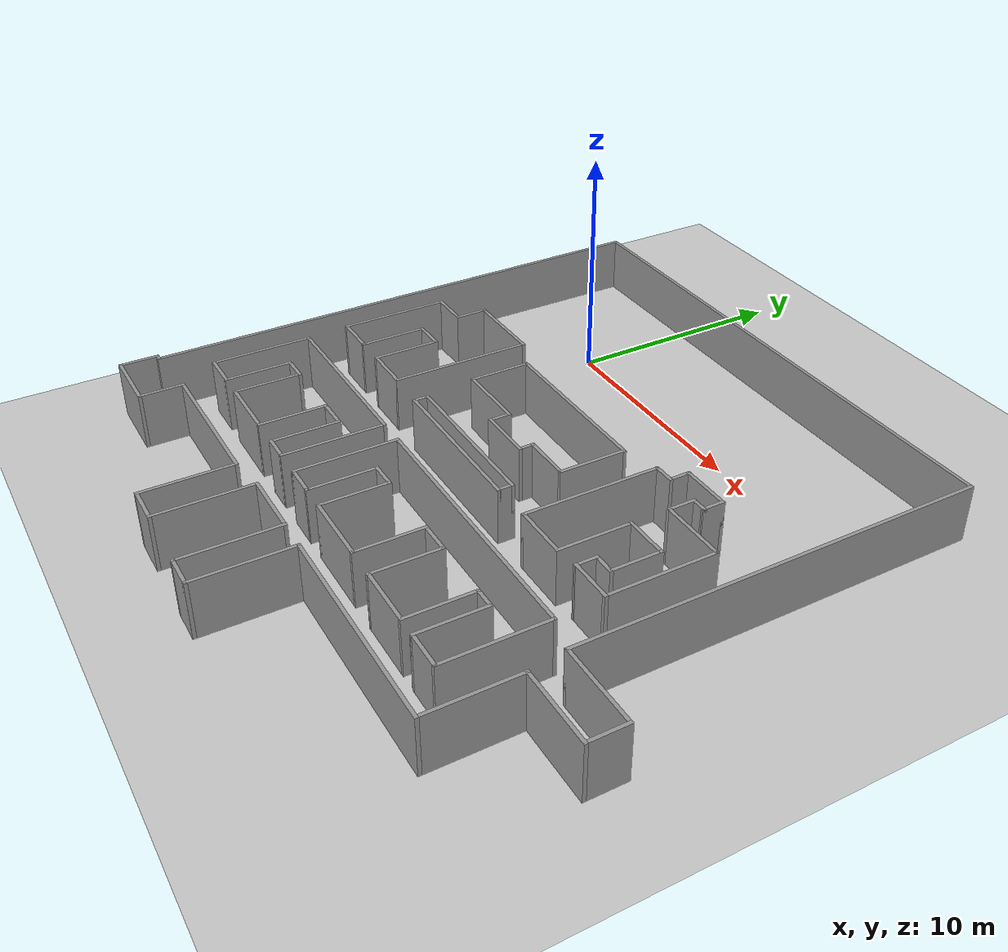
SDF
<?xml version="1.0"?>
<sdf version='1.7'>
  <world name='default'>
    <light name='sun' type='directional'>
      <cast_shadows>1</cast_shadows>
      <pose>0 0 10 0 -0 0</pose>
      <diffuse>0.8 0.8 0.8 1</diffuse>
      <specular>0.2 0.2 0.2 1</specular>
      <attenuation>
        <range>1000</range>
        <constant>0.9</constant>
        <linear>0.01</linear>
        <quadratic>0.001</quadratic>
      </attenuation>
      <direction>-0.5 0.1 -0.9</direction>
      <spot>
        <inner_angle>0</inner_angle>
        <outer_angle>0</outer_angle>
        <falloff>0</falloff>
      </spot>
    </light>
    <model name='ground_plane'>
      <static>1</static>
      <link name='link'>
        <collision name='collision'>
          <geometry>
            <plane>
              <normal>0 0 1</normal>
              <size>100 100</size>
            </plane>
          </geometry>
          <surface>
            <contact>
              <collide_bitmask>65535</collide_bitmask>
              <ode/>
            </contact>
            <friction>
              <ode>
                <mu>100</mu>
                <mu2>50</mu2>
              </ode>
              <torsional>
                <ode/>
              </torsional>
            </friction>
            <bounce/>
          </surface>
          <max_contacts>10</max_contacts>
        </collision>
        <visual name='visual'>
          <cast_shadows>0</cast_shadows>
          <geometry>
            <plane>
              <normal>0 0 1</normal>
              <size>100 100</size>
            </plane>
          </geometry>
          <material>
            <script>
              <uri>file://media/materials/scripts/gazebo.material</uri>
              <name>Gazebo/Grey</name>
            </script>
          </material>
        </visual>
        <self_collide>0</self_collide>
        <enable_wind>0</enable_wind>
        <kinematic>0</kinematic>
      </link>
    </model>
    <magnetic_field>6e-06 2.3e-05 -4.2e-05</magnetic_field>
    <atmosphere type='adiabatic'/>
    <!-- Gravity and physics: as empty.world, which says why. Keep the two in step. -->
    <gravity>0 0 -9.80665</gravity>
    <physics name="1ms" type="ode" default="true">
      <max_step_size>0.001</max_step_size>
      <real_time_factor>1</real_time_factor>
      <real_time_update_rate>1000</real_time_update_rate>
      <ode>
        <solver>
          <type>quick</type>
          <iters>50</iters>
          <sor>1.3</sor>
          <island_threads>4</island_threads>
          <friction_model>cone_model</friction_model>
        </solver>
        <constraints>
          <cfm>0</cfm>
          <erp>0.2</erp>
          <contact_max_correcting_vel>100</contact_max_correcting_vel>
          <contact_surface_layer>0.001</contact_surface_layer>
        </constraints>
      </ode>
    </physics>
    <plugin name="real_time_lock" filename="librover_sim_real_time_lock.so">
      <time_constant>0.5</time_constant>
      <max_boost>0.5</max_boost>
      <max_lag>0.5</max_lag>
    </plugin>
    <scene>
      <ambient>0.4 0.4 0.4 1</ambient>
      <background>0.7 0.7 0.7 1</background>
      <shadows>1</shadows>
    </scene>
    <audio>
      <device>default</device>
    </audio>
    <wind/>
    <spherical_coordinates>
      <surface_model>EARTH_WGS84</surface_model>
      <latitude_deg>0</latitude_deg>
      <longitude_deg>0</longitude_deg>
      <elevation>0</elevation>
      <heading_deg>0</heading_deg>
    </spherical_coordinates>
    <model name='ACL_office_simple'>
      <pose>7.7557 -8.2982 0 0 -0 0</pose>
      <link name='Wall_0'>
        <collision name='Wall_0_Collision'>
          <geometry>
            <box>
              <size>23.6998 0.15 2.5</size>
            </box>
          </geometry>
          <pose>0 0 1.25 0 -0 0</pose>
          <max_contacts>10</max_contacts>
          <surface>
            <contact>
              <ode/>
            </contact>
            <bounce/>
            <friction>
              <torsional>
                <ode/>
              </torsional>
              <ode/>
            </friction>
          </surface>
        </collision>
        <visual name='Wall_0_Visual'>
          <pose>0 0 1.25 0 -0 0</pose>
          <geometry>
            <box>
              <size>23.6998 0.15 2.5</size>
            </box>
          </geometry>
          <material>
            <script>
              <uri>file://media/materials/scripts/gazebo.material</uri>
              <name>Gazebo/Grey</name>
            </script>
            <ambient>1 1 1 1</ambient>
          </material>
          <meta>
            <layer>0</layer>
          </meta>
        </visual>
        <pose>-13.7248 1.80009 0 0 -0 -1.57078</pose>
        <self_collide>0</self_collide>
        <enable_wind>0</enable_wind>
        <kinematic>0</kinematic>
      </link>
      <link name='Wall_10'>
        <collision name='Wall_10_Collision'>
          <geometry>
            <box>
              <size>9.5 0.15 2.5</size>
            </box>
          </geometry>
          <pose>0 0 1.25 0 -0 0</pose>
          <max_contacts>10</max_contacts>
          <surface>
            <contact>
              <ode/>
            </contact>
            <bounce/>
            <friction>
              <torsional>
                <ode/>
              </torsional>
              <ode/>
            </friction>
          </surface>
        </collision>
        <visual name='Wall_10_Visual'>
          <pose>0 0 1.25 0 -0 0</pose>
          <geometry>
            <box>
              <size>9.5 0.15 2.5</size>
            </box>
          </geometry>
          <material>
            <script>
              <uri>file://media/materials/scripts/gazebo.material</uri>
              <name>Gazebo/Grey</name>
            </script>
            <ambient>1 1 1 1</ambient>
          </material>
          <meta>
            <layer>0</layer>
          </meta>
        </visual>
        <pose>5.95001 -9.475 0 0 -0 3.14159</pose>
        <self_collide>0</self_collide>
        <enable_wind>0</enable_wind>
        <kinematic>0</kinematic>
      </link>
      <link name='Wall_100'>
        <collision name='Wall_100_Collision'>
          <geometry>
            <box>
              <size>3 0.15 2.5</size>
            </box>
          </geometry>
          <pose>0 0 1.25 0 -0 0</pose>
          <max_contacts>10</max_contacts>
          <surface>
            <contact>
              <ode/>
            </contact>
            <bounce/>
            <friction>
              <torsional>
                <ode/>
              </torsional>
              <ode/>
            </friction>
          </surface>
        </collision>
        <visual name='Wall_100_Visual'>
          <pose>0 0 1.25 0 -0 0</pose>
          <geometry>
            <box>
              <size>3 0.15 2.5</size>
            </box>
          </geometry>
          <material>
            <script>
              <uri>file://media/materials/scripts/gazebo.material</uri>
              <name>Gazebo/Grey</name>
            </script>
            <ambient>1 1 1 1</ambient>
          </material>
          <meta>
            <layer>0</layer>
          </meta>
        </visual>
        <pose>2.02363 2.21088 0 0 -0 1.5708</pose>
        <self_collide>0</self_collide>
        <enable_wind>0</enable_wind>
        <kinematic>0</kinematic>
      </link>
      <link name='Wall_101'>
        <collision name='Wall_101_Collision'>
          <geometry>
            <box>
              <size>7.7 0.15 2.5</size>
            </box>
          </geometry>
          <pose>0 0 1.25 0 -0 0</pose>
          <max_contacts>10</max_contacts>
          <surface>
            <contact>
              <ode/>
            </contact>
            <bounce/>
            <friction>
              <torsional>
                <ode/>
              </torsional>
              <ode/>
            </friction>
          </surface>
        </collision>
        <visual name='Wall_101_Visual'>
          <pose>0 0 1.25 0 -0 0</pose>
          <geometry>
            <box>
              <size>7.7 0.15 2.5</size>
            </box>
          </geometry>
          <material>
            <script>
              <uri>file://media/materials/scripts/gazebo.material</uri>
              <name>Gazebo/Grey</name>
            </script>
            <ambient>1 1 1 1</ambient>
          </material>
          <meta>
            <layer>0</layer>
          </meta>
        </visual>
        <pose>-1.75137 3.63588 0 0 -0 3.14159</pose>
        <self_collide>0</self_collide>
        <enable_wind>0</enable_wind>
        <kinematic>0</kinematic>
      </link>
      <link name='Wall_11'>
        <collision name='Wall_11_Collision'>
          <geometry>
            <box>
              <size>4.25 0.15 2.5</size>
            </box>
          </geometry>
          <pose>0 0 1.25 0 -0 0</pose>
          <max_contacts>10</max_contacts>
          <surface>
            <contact>
              <ode/>
            </contact>
            <bounce/>
            <friction>
              <torsional>
                <ode/>
              </torsional>
              <ode/>
            </friction>
          </surface>
        </collision>
        <visual name='Wall_11_Visual'>
          <pose>0 0 1.25 0 -0 0</pose>
          <geometry>
            <box>
              <size>4.25 0.15 2.5</size>
            </box>
          </geometry>
          <material>
            <script>
              <uri>file://media/materials/scripts/gazebo.material</uri>
              <name>Gazebo/Grey</name>
            </script>
            <ambient>1 1 1 1</ambient>
          </material>
          <meta>
            <layer>0</layer>
          </meta>
        </visual>
        <pose>1.27501 -11.525 0 0 -0 -1.5708</pose>
        <self_collide>0</self_collide>
        <enable_wind>0</enable_wind>
        <kinematic>0</kinematic>
      </link>
      <link name='Wall_12'>
        <collision name='Wall_12_Collision'>
          <geometry>
            <box>
              <size>1.5 0.15 2.5</size>
            </box>
          </geometry>
          <pose>0 0 1.25 0 -0 0</pose>
          <max_contacts>10</max_contacts>
          <surface>
            <contact>
              <ode/>
            </contact>
            <bounce/>
            <friction>
              <torsional>
                <ode/>
              </torsional>
              <ode/>
            </friction>
          </surface>
        </collision>
        <visual name='Wall_12_Visual'>
          <pose>0 0 1.25 0 -0 0</pose>
          <geometry>
            <box>
              <size>1.5 0.15 2.5</size>
            </box>
          </geometry>
          <material>
            <script>
              <uri>file://media/materials/scripts/gazebo.material</uri>
              <name>Gazebo/Grey</name>
            </script>
            <ambient>1 1 1 1</ambient>
          </material>
          <meta>
            <layer>0</layer>
          </meta>
        </visual>
        <pose>0.600008 -13.575 0 0 -0 3.14159</pose>
        <self_collide>0</self_collide>
        <enable_wind>0</enable_wind>
        <kinematic>0</kinematic>
      </link>
      <link name='Wall_13'>
        <collision name='Wall_13_Collision'>
          <geometry>
            <box>
              <size>4.25 0.15 2.5</size>
            </box>
          </geometry>
          <pose>0 0 1.25 0 -0 0</pose>
          <max_contacts>10</max_contacts>
          <surface>
            <contact>
              <ode/>
            </contact>
            <bounce/>
            <friction>
              <torsional>
                <ode/>
              </torsional>
              <ode/>
            </friction>
          </surface>
        </collision>
        <visual name='Wall_13_Visual'>
          <pose>0 0 1.25 0 -0 0</pose>
          <geometry>
            <box>
              <size>4.25 0.15 2.5</size>
            </box>
          </geometry>
          <material>
            <script>
              <uri>file://media/materials/scripts/gazebo.material</uri>
              <name>Gazebo/Grey</name>
            </script>
            <ambient>1 1 1 1</ambient>
          </material>
          <meta>
            <layer>0</layer>
          </meta>
        </visual>
        <pose>-0.074992 -11.525 0 0 -0 1.5708</pose>
        <self_collide>0</self_collide>
        <enable_wind>0</enable_wind>
        <kinematic>0</kinematic>
      </link>
      <link name='Wall_14'>
        <collision name='Wall_14_Collision'>
          <geometry>
            <box>
              <size>3 0.15 2.5</size>
            </box>
          </geometry>
          <pose>0 0 1.25 0 -0 0</pose>
          <max_contacts>10</max_contacts>
          <surface>
            <contact>
              <ode/>
            </contact>
            <bounce/>
            <friction>
              <torsional>
                <ode/>
              </torsional>
              <ode/>
            </friction>
          </surface>
        </collision>
        <visual name='Wall_14_Visual'>
          <pose>0 0 1.25 0 -0 0</pose>
          <geometry>
            <box>
              <size>3 0.15 2.5</size>
            </box>
          </geometry>
          <material>
            <script>
              <uri>file://media/materials/scripts/gazebo.material</uri>
              <name>Gazebo/Grey</name>
            </script>
            <ambient>1 1 1 1</ambient>
          </material>
          <meta>
            <layer>0</layer>
          </meta>
        </visual>
        <pose>-1.49999 -9.475 0 0 -0 3.14159</pose>
        <self_collide>0</self_collide>
        <enable_wind>0</enable_wind>
        <kinematic>0</kinematic>
      </link>
      <link name='Wall_15'>
        <collision name='Wall_15_Collision'>
          <geometry>
            <box>
              <size>4.25 0.15 2.5</size>
            </box>
          </geometry>
          <pose>0 0 1.25 0 -0 0</pose>
          <max_contacts>10</max_contacts>
          <surface>
            <contact>
              <ode/>
            </contact>
            <bounce/>
            <friction>
              <torsional>
                <ode/>
              </torsional>
              <ode/>
            </friction>
          </surface>
        </collision>
        <visual name='Wall_15_Visual'>
          <pose>0 0 1.25 0 -0 0</pose>
          <geometry>
            <box>
              <size>4.25 0.15 2.5</size>
            </box>
          </geometry>
          <material>
            <script>
              <uri>file://media/materials/scripts/gazebo.material</uri>
              <name>Gazebo/Grey</name>
            </script>
            <ambient>1 1 1 1</ambient>
          </material>
          <meta>
            <layer>0</layer>
          </meta>
        </visual>
        <pose>-2.92499 -11.525 0 0 -0 -1.5708</pose>
        <self_collide>0</self_collide>
        <enable_wind>0</enable_wind>
        <kinematic>0</kinematic>
      </link>
      <link name='Wall_16'>
        <collision name='Wall_16_Collision'>
          <geometry>
            <box>
              <size>1.75 0.15 2.5</size>
            </box>
          </geometry>
          <pose>0 0 1.25 0 -0 0</pose>
          <max_contacts>10</max_contacts>
          <surface>
            <contact>
              <ode/>
            </contact>
            <bounce/>
            <friction>
              <torsional>
                <ode/>
              </torsional>
              <ode/>
            </friction>
          </surface>
        </collision>
        <visual name='Wall_16_Visual'>
          <pose>0 0 1.25 0 -0 0</pose>
          <geometry>
            <box>
              <size>1.75 0.15 2.5</size>
            </box>
          </geometry>
          <material>
            <script>
              <uri>file://media/materials/scripts/gazebo.material</uri>
              <name>Gazebo/Grey</name>
            </script>
            <ambient>1 1 1 1</ambient>
          </material>
          <meta>
            <layer>0</layer>
          </meta>
        </visual>
        <pose>-3.72499 -13.575 0 0 -0 3.14159</pose>
        <self_collide>0</self_collide>
        <enable_wind>0</enable_wind>
        <kinematic>0</kinematic>
      </link>
      <link name='Wall_17'>
        <collision name='Wall_17_Collision'>
          <geometry>
            <box>
              <size>4 0.15 2.5</size>
            </box>
          </geometry>
          <pose>0 0 1.25 0 -0 0</pose>
          <max_contacts>10</max_contacts>
          <surface>
            <contact>
              <ode/>
            </contact>
            <bounce/>
            <friction>
              <torsional>
                <ode/>
              </torsional>
              <ode/>
            </friction>
          </surface>
        </collision>
        <visual name='Wall_17_Visual'>
          <pose>0 0 1.25 0 -0 0</pose>
          <geometry>
            <box>
              <size>4 0.15 2.5</size>
            </box>
          </geometry>
          <material>
            <script>
              <uri>file://media/materials/scripts/gazebo.material</uri>
              <name>Gazebo/Grey</name>
            </script>
            <ambient>1 1 1 1</ambient>
          </material>
          <meta>
            <layer>0</layer>
          </meta>
        </visual>
        <pose>-4.52499 -11.65 0 0 -0 1.5708</pose>
        <self_collide>0</self_collide>
        <enable_wind>0</enable_wind>
        <kinematic>0</kinematic>
      </link>
      <link name='Wall_18'>
        <collision name='Wall_18_Collision'>
          <geometry>
            <box>
              <size>6.75 0.15 2.5</size>
            </box>
          </geometry>
          <pose>0 0 1.25 0 -0 0</pose>
          <max_contacts>10</max_contacts>
          <surface>
            <contact>
              <ode/>
            </contact>
            <bounce/>
            <friction>
              <torsional>
                <ode/>
              </torsional>
              <ode/>
            </friction>
          </surface>
        </collision>
        <visual name='Wall_18_Visual'>
          <pose>0 0 1.25 0 -0 0</pose>
          <geometry>
            <box>
              <size>6.75 0.15 2.5</size>
            </box>
          </geometry>
          <material>
            <script>
              <uri>file://media/materials/scripts/gazebo.material</uri>
              <name>Gazebo/Grey</name>
            </script>
            <ambient>1 1 1 1</ambient>
          </material>
          <meta>
            <layer>0</layer>
          </meta>
        </visual>
        <pose>-7.82499 -9.725 0 0 -0 3.14159</pose>
        <self_collide>0</self_collide>
        <enable_wind>0</enable_wind>
        <kinematic>0</kinematic>
      </link>
      <link name='Wall_19'>
        <collision name='Wall_19_Collision'>
          <geometry>
            <box>
              <size>2 0.15 2.5</size>
            </box>
          </geometry>
          <pose>0 0 1.25 0 -0 0</pose>
          <max_contacts>10</max_contacts>
          <surface>
            <contact>
              <ode/>
            </contact>
            <bounce/>
            <friction>
              <torsional>
                <ode/>
              </torsional>
              <ode/>
            </friction>
          </surface>
        </collision>
        <visual name='Wall_19_Visual'>
          <pose>0 0 1.25 0 -0 0</pose>
          <geometry>
            <box>
              <size>2 0.15 2.5</size>
            </box>
          </geometry>
          <material>
            <script>
              <uri>file://media/materials/scripts/gazebo.material</uri>
              <name>Gazebo/Grey</name>
            </script>
            <ambient>1 1 1 1</ambient>
          </material>
          <meta>
            <layer>0</layer>
          </meta>
        </visual>
        <pose>-11.125 -10.65 0 0 -0 -1.5708</pose>
        <self_collide>0</self_collide>
        <enable_wind>0</enable_wind>
        <kinematic>0</kinematic>
      </link>
      <link name='Wall_2'>
        <collision name='Wall_2_Collision'>
          <geometry>
            <box>
              <size>24.25 0.15 2.5</size>
            </box>
          </geometry>
          <pose>0 0 1.25 0 -0 0</pose>
          <max_contacts>10</max_contacts>
          <surface>
            <contact>
              <ode/>
            </contact>
            <bounce/>
            <friction>
              <torsional>
                <ode/>
              </torsional>
              <ode/>
            </friction>
          </surface>
        </collision>
        <visual name='Wall_2_Visual'>
          <pose>0 0 1.25 0 -0 0</pose>
          <geometry>
            <box>
              <size>24.25 0.15 2.5</size>
            </box>
          </geometry>
          <material>
            <script>
              <uri>file://media/materials/scripts/gazebo.material</uri>
              <name>Gazebo/Grey</name>
            </script>
            <ambient>1 1 1 1</ambient>
          </material>
          <meta>
            <layer>0</layer>
          </meta>
        </visual>
        <pose>-1.67499 13.575 0 0 -0 0</pose>
        <self_collide>0</self_collide>
        <enable_wind>0</enable_wind>
        <kinematic>0</kinematic>
      </link>
      <link name='Wall_20'>
        <collision name='Wall_20_Collision'>
          <geometry>
            <box>
              <size>3 0.15 2.5</size>
            </box>
          </geometry>
          <pose>0 0 1.25 0 -0 0</pose>
          <max_contacts>10</max_contacts>
          <surface>
            <contact>
              <ode/>
            </contact>
            <bounce/>
            <friction>
              <torsional>
                <ode/>
              </torsional>
              <ode/>
            </friction>
          </surface>
        </collision>
        <visual name='Wall_20_Visual'>
          <pose>0 0 1.25 0 -0 0</pose>
          <geometry>
            <box>
              <size>3 0.15 2.5</size>
            </box>
          </geometry>
          <material>
            <script>
              <uri>file://media/materials/scripts/gazebo.material</uri>
              <name>Gazebo/Grey</name>
            </script>
            <ambient>1 1 1 1</ambient>
          </material>
          <meta>
            <layer>0</layer>
          </meta>
        </visual>
        <pose>-12.55 -11.575 0 0 -0 3.14159</pose>
        <self_collide>0</self_collide>
        <enable_wind>0</enable_wind>
        <kinematic>0</kinematic>
      </link>
      <link name='Wall_23'>
        <collision name='Wall_23_Collision'>
          <geometry>
            <box>
              <size>1.75 0.15 2.5</size>
            </box>
          </geometry>
          <pose>0 0 1.25 0 -0 0</pose>
          <max_contacts>10</max_contacts>
          <surface>
            <contact>
              <ode/>
            </contact>
            <bounce/>
            <friction>
              <torsional>
                <ode/>
              </torsional>
              <ode/>
            </friction>
          </surface>
        </collision>
        <visual name='Wall_23_Visual'>
          <pose>0 0 1.25 0 -0 0</pose>
          <geometry>
            <box>
              <size>1.75 0.15 2.5</size>
            </box>
          </geometry>
          <material>
            <script>
              <uri>file://media/materials/scripts/gazebo.material</uri>
              <name>Gazebo/Grey</name>
            </script>
            <ambient>1 1 1 1</ambient>
          </material>
          <meta>
            <layer>0</layer>
          </meta>
        </visual>
        <pose>-13.9748 -10.7749 0 0 -0 1.57059</pose>
        <self_collide>0</self_collide>
        <enable_wind>0</enable_wind>
        <kinematic>0</kinematic>
      </link>
      <link name='Wall_24'>
        <collision name='Wall_24_Collision'>
          <geometry>
            <box>
              <size>0.4 0.15 2.5</size>
            </box>
          </geometry>
          <pose>0 0 1.25 0 -0 0</pose>
          <max_contacts>10</max_contacts>
          <surface>
            <contact>
              <ode/>
            </contact>
            <bounce/>
            <friction>
              <torsional>
                <ode/>
              </torsional>
              <ode/>
            </friction>
          </surface>
        </collision>
        <visual name='Wall_24_Visual'>
          <pose>0 0 1.25 0 -0 0</pose>
          <geometry>
            <box>
              <size>0.4 0.15 2.5</size>
            </box>
          </geometry>
          <material>
            <script>
              <uri>file://media/materials/scripts/gazebo.material</uri>
              <name>Gazebo/Grey</name>
            </script>
            <ambient>1 1 1 1</ambient>
          </material>
          <meta>
            <layer>0</layer>
          </meta>
        </visual>
        <pose>-13.8497 -9.97483 0 0 -0 0</pose>
        <self_collide>0</self_collide>
        <enable_wind>0</enable_wind>
        <kinematic>0</kinematic>
      </link>
      <link name='Wall_27'>
        <collision name='Wall_27_Collision'>
          <geometry>
            <box>
              <size>4.5 0.15 2.5</size>
            </box>
          </geometry>
          <pose>0 0 1.25 0 -0 0</pose>
          <max_contacts>10</max_contacts>
          <surface>
            <contact>
              <ode/>
            </contact>
            <bounce/>
            <friction>
              <torsional>
                <ode/>
              </torsional>
              <ode/>
            </friction>
          </surface>
        </collision>
        <visual name='Wall_27_Visual'>
          <pose>0 0 1.25 0 -0 0</pose>
          <geometry>
            <box>
              <size>4.5 0.15 2.5</size>
            </box>
          </geometry>
          <material>
            <script>
              <uri>file://media/materials/scripts/gazebo.material</uri>
              <name>Gazebo/Grey</name>
            </script>
            <ambient>1 1 1 1</ambient>
          </material>
          <meta>
            <layer>0</layer>
          </meta>
        </visual>
        <pose>-12.2186 -5.84008 0 0 -0 -1.5708</pose>
        <self_collide>0</self_collide>
        <enable_wind>0</enable_wind>
        <kinematic>0</kinematic>
      </link>
      <link name='Wall_28'>
        <collision name='Wall_28_Collision'>
          <geometry>
            <box>
              <size>1.75 0.15 2.5</size>
            </box>
          </geometry>
          <pose>0 0 1.25 0 -0 0</pose>
          <max_contacts>10</max_contacts>
          <surface>
            <contact>
              <ode/>
            </contact>
            <bounce/>
            <friction>
              <torsional>
                <ode/>
              </torsional>
              <ode/>
            </friction>
          </surface>
        </collision>
        <visual name='Wall_28_Visual'>
          <pose>0 0 1.25 0 -0 0</pose>
          <geometry>
            <box>
              <size>1.75 0.15 2.5</size>
            </box>
          </geometry>
          <material>
            <script>
              <uri>file://media/materials/scripts/gazebo.material</uri>
              <name>Gazebo/Grey</name>
            </script>
            <ambient>1 1 1 1</ambient>
          </material>
          <meta>
            <layer>0</layer>
          </meta>
        </visual>
        <pose>-11.4186 -8.01508 0 0 -0 0</pose>
        <self_collide>0</self_collide>
        <enable_wind>0</enable_wind>
        <kinematic>0</kinematic>
      </link>
      <link name='Wall_29'>
        <collision name='Wall_29_Collision'>
          <geometry>
            <box>
              <size>3 0.15 2.5</size>
            </box>
          </geometry>
          <pose>0 0 1.25 0 -0 0</pose>
          <max_contacts>10</max_contacts>
          <surface>
            <contact>
              <ode/>
            </contact>
            <bounce/>
            <friction>
              <torsional>
                <ode/>
              </torsional>
              <ode/>
            </friction>
          </surface>
        </collision>
        <visual name='Wall_29_Visual'>
          <pose>0 0 1.25 0 -0 0</pose>
          <geometry>
            <box>
              <size>3 0.15 2.5</size>
            </box>
          </geometry>
          <material>
            <script>
              <uri>file://media/materials/scripts/gazebo.material</uri>
              <name>Gazebo/Grey</name>
            </script>
            <ambient>1 1 1 1</ambient>
          </material>
          <meta>
            <layer>0</layer>
          </meta>
        </visual>
        <pose>-10.6186 -6.59008 0 0 -0 1.5708</pose>
        <self_collide>0</self_collide>
        <enable_wind>0</enable_wind>
        <kinematic>0</kinematic>
      </link>
      <link name='Wall_3'>
        <collision name='Wall_3_Collision'>
          <geometry>
            <box>
              <size>17.75 0.15 2.5</size>
            </box>
          </geometry>
          <pose>0 0 1.25 0 -0 0</pose>
          <max_contacts>10</max_contacts>
          <surface>
            <contact>
              <ode/>
            </contact>
            <bounce/>
            <friction>
              <torsional>
                <ode/>
              </torsional>
              <ode/>
            </friction>
          </surface>
        </collision>
        <visual name='Wall_3_Visual'>
          <pose>0 0 1.25 0 -0 0</pose>
          <geometry>
            <box>
              <size>17.75 0.15 2.5</size>
            </box>
          </geometry>
          <material>
            <script>
              <uri>file://media/materials/scripts/gazebo.material</uri>
              <name>Gazebo/Grey</name>
            </script>
            <ambient>1 1 1 1</ambient>
          </material>
          <meta>
            <layer>0</layer>
          </meta>
        </visual>
        <pose>10.375 4.775 0 0 -0 -1.5708</pose>
        <self_collide>0</self_collide>
        <enable_wind>0</enable_wind>
        <kinematic>0</kinematic>
      </link>
      <link name='Wall_30'>
        <collision name='Wall_30_Collision'>
          <geometry>
            <box>
              <size>1.25 0.15 2.5</size>
            </box>
          </geometry>
          <pose>0 0 1.25 0 -0 0</pose>
          <max_contacts>10</max_contacts>
          <surface>
            <contact>
              <ode/>
            </contact>
            <bounce/>
            <friction>
              <torsional>
                <ode/>
              </torsional>
              <ode/>
            </friction>
          </surface>
        </collision>
        <visual name='Wall_30_Visual'>
          <pose>0 0 1.25 0 -0 0</pose>
          <geometry>
            <box>
              <size>1.25 0.15 2.5</size>
            </box>
          </geometry>
          <material>
            <script>
              <uri>file://media/materials/scripts/gazebo.material</uri>
              <name>Gazebo/Grey</name>
            </script>
            <ambient>1 1 1 1</ambient>
          </material>
          <meta>
            <layer>0</layer>
          </meta>
        </visual>
        <pose>-10.0686 -5.16508 0 0 -0 0</pose>
        <self_collide>0</self_collide>
        <enable_wind>0</enable_wind>
        <kinematic>0</kinematic>
      </link>
      <link name='Wall_31'>
        <collision name='Wall_31_Collision'>
          <geometry>
            <box>
              <size>3 0.15 2.5</size>
            </box>
          </geometry>
          <pose>0 0 1.25 0 -0 0</pose>
          <max_contacts>10</max_contacts>
          <surface>
            <contact>
              <ode/>
            </contact>
            <bounce/>
            <friction>
              <torsional>
                <ode/>
              </torsional>
              <ode/>
            </friction>
          </surface>
        </collision>
        <visual name='Wall_31_Visual'>
          <pose>0 0 1.25 0 -0 0</pose>
          <geometry>
            <box>
              <size>3 0.15 2.5</size>
            </box>
          </geometry>
          <material>
            <script>
              <uri>file://media/materials/scripts/gazebo.material</uri>
              <name>Gazebo/Grey</name>
            </script>
            <ambient>1 1 1 1</ambient>
          </material>
          <meta>
            <layer>0</layer>
          </meta>
        </visual>
        <pose>-9.51863 -6.59008 0 0 -0 -1.5708</pose>
        <self_collide>0</self_collide>
        <enable_wind>0</enable_wind>
        <kinematic>0</kinematic>
      </link>
      <link name='Wall_32'>
        <collision name='Wall_32_Collision'>
          <geometry>
            <box>
              <size>3 0.15 2.5</size>
            </box>
          </geometry>
          <pose>0 0 1.25 0 -0 0</pose>
          <max_contacts>10</max_contacts>
          <surface>
            <contact>
              <ode/>
            </contact>
            <bounce/>
            <friction>
              <torsional>
                <ode/>
              </torsional>
              <ode/>
            </friction>
          </surface>
        </collision>
        <visual name='Wall_32_Visual'>
          <pose>0 0 1.25 0 -0 0</pose>
          <geometry>
            <box>
              <size>3 0.15 2.5</size>
            </box>
          </geometry>
          <material>
            <script>
              <uri>file://media/materials/scripts/gazebo.material</uri>
              <name>Gazebo/Grey</name>
            </script>
            <ambient>1 1 1 1</ambient>
          </material>
          <meta>
            <layer>0</layer>
          </meta>
        </visual>
        <pose>-8.09363 -8.01508 0 0 -0 0</pose>
        <self_collide>0</self_collide>
        <enable_wind>0</enable_wind>
        <kinematic>0</kinematic>
      </link>
      <link name='Wall_33'>
        <collision name='Wall_33_Collision'>
          <geometry>
            <box>
              <size>3 0.15 2.5</size>
            </box>
          </geometry>
          <pose>0 0 1.25 0 -0 0</pose>
          <max_contacts>10</max_contacts>
          <surface>
            <contact>
              <ode/>
            </contact>
            <bounce/>
            <friction>
              <torsional>
                <ode/>
              </torsional>
              <ode/>
            </friction>
          </surface>
        </collision>
        <visual name='Wall_33_Visual'>
          <pose>0 0 1.25 0 -0 0</pose>
          <geometry>
            <box>
              <size>3 0.15 2.5</size>
            </box>
          </geometry>
          <material>
            <script>
              <uri>file://media/materials/scripts/gazebo.material</uri>
              <name>Gazebo/Grey</name>
            </script>
            <ambient>1 1 1 1</ambient>
          </material>
          <meta>
            <layer>0</layer>
          </meta>
        </visual>
        <pose>-6.66863 -6.59008 0 0 -0 1.5708</pose>
        <self_collide>0</self_collide>
        <enable_wind>0</enable_wind>
        <kinematic>0</kinematic>
      </link>
      <link name='Wall_34'>
        <collision name='Wall_34_Collision'>
          <geometry>
            <box>
              <size>1.5 0.15 2.5</size>
            </box>
          </geometry>
          <pose>0 0 1.25 0 -0 0</pose>
          <max_contacts>10</max_contacts>
          <surface>
            <contact>
              <ode/>
            </contact>
            <bounce/>
            <friction>
              <torsional>
                <ode/>
              </torsional>
              <ode/>
            </friction>
          </surface>
        </collision>
        <visual name='Wall_34_Visual'>
          <pose>0 0 1.25 0 -0 0</pose>
          <geometry>
            <box>
              <size>1.5 0.15 2.5</size>
            </box>
          </geometry>
          <material>
            <script>
              <uri>file://media/materials/scripts/gazebo.material</uri>
              <name>Gazebo/Grey</name>
            </script>
            <ambient>1 1 1 1</ambient>
          </material>
          <meta>
            <layer>0</layer>
          </meta>
        </visual>
        <pose>-5.99363 -5.16508 0 0 -0 0</pose>
        <self_collide>0</self_collide>
        <enable_wind>0</enable_wind>
        <kinematic>0</kinematic>
      </link>
      <link name='Wall_35'>
        <collision name='Wall_35_Collision'>
          <geometry>
            <box>
              <size>3 0.15 2.5</size>
            </box>
          </geometry>
          <pose>0 0 1.25 0 -0 0</pose>
          <max_contacts>10</max_contacts>
          <surface>
            <contact>
              <ode/>
            </contact>
            <bounce/>
            <friction>
              <torsional>
                <ode/>
              </torsional>
              <ode/>
            </friction>
          </surface>
        </collision>
        <visual name='Wall_35_Visual'>
          <pose>0 0 1.25 0 -0 0</pose>
          <geometry>
            <box>
              <size>3 0.15 2.5</size>
            </box>
          </geometry>
          <material>
            <script>
              <uri>file://media/materials/scripts/gazebo.material</uri>
              <name>Gazebo/Grey</name>
            </script>
            <ambient>1 1 1 1</ambient>
          </material>
          <meta>
            <layer>0</layer>
          </meta>
        </visual>
        <pose>-5.31863 -6.59008 0 0 -0 -1.5708</pose>
        <self_collide>0</self_collide>
        <enable_wind>0</enable_wind>
        <kinematic>0</kinematic>
      </link>
      <link name='Wall_36'>
        <collision name='Wall_36_Collision'>
          <geometry>
            <box>
              <size>1.25 0.15 2.5</size>
            </box>
          </geometry>
          <pose>0 0 1.25 0 -0 0</pose>
          <max_contacts>10</max_contacts>
          <surface>
            <contact>
              <ode/>
            </contact>
            <bounce/>
            <friction>
              <torsional>
                <ode/>
              </torsional>
              <ode/>
            </friction>
          </surface>
        </collision>
        <visual name='Wall_36_Visual'>
          <pose>0 0 1.25 0 -0 0</pose>
          <geometry>
            <box>
              <size>1.25 0.15 2.5</size>
            </box>
          </geometry>
          <material>
            <script>
              <uri>file://media/materials/scripts/gazebo.material</uri>
              <name>Gazebo/Grey</name>
            </script>
            <ambient>1 1 1 1</ambient>
          </material>
          <meta>
            <layer>0</layer>
          </meta>
        </visual>
        <pose>-4.76863 -8.01508 0 0 -0 0</pose>
        <self_collide>0</self_collide>
        <enable_wind>0</enable_wind>
        <kinematic>0</kinematic>
      </link>
      <link name='Wall_37'>
        <collision name='Wall_37_Collision'>
          <geometry>
            <box>
              <size>4.5 0.15 2.5</size>
            </box>
          </geometry>
          <pose>0 0 1.25 0 -0 0</pose>
          <max_contacts>10</max_contacts>
          <surface>
            <contact>
              <ode/>
            </contact>
            <bounce/>
            <friction>
              <torsional>
                <ode/>
              </torsional>
              <ode/>
            </friction>
          </surface>
        </collision>
        <visual name='Wall_37_Visual'>
          <pose>0 0 1.25 0 -0 0</pose>
          <geometry>
            <box>
              <size>4.5 0.15 2.5</size>
            </box>
          </geometry>
          <material>
            <script>
              <uri>file://media/materials/scripts/gazebo.material</uri>
              <name>Gazebo/Grey</name>
            </script>
            <ambient>1 1 1 1</ambient>
          </material>
          <meta>
            <layer>0</layer>
          </meta>
        </visual>
        <pose>-4.21863 -5.84008 0 0 -0 1.5708</pose>
        <self_collide>0</self_collide>
        <enable_wind>0</enable_wind>
        <kinematic>0</kinematic>
      </link>
      <link name='Wall_38'>
        <collision name='Wall_38_Collision'>
          <geometry>
            <box>
              <size>8.15 0.15 2.5</size>
            </box>
          </geometry>
          <pose>0 0 1.25 0 -0 0</pose>
          <max_contacts>10</max_contacts>
          <surface>
            <contact>
              <ode/>
            </contact>
            <bounce/>
            <friction>
              <torsional>
                <ode/>
              </torsional>
              <ode/>
            </friction>
          </surface>
        </collision>
        <visual name='Wall_38_Visual'>
          <pose>0 0 1.25 0 -0 0</pose>
          <geometry>
            <box>
              <size>8.15 0.15 2.5</size>
            </box>
          </geometry>
          <material>
            <script>
              <uri>file://media/materials/scripts/gazebo.material</uri>
              <name>Gazebo/Grey</name>
            </script>
            <ambient>1 1 1 1</ambient>
          </material>
          <meta>
            <layer>0</layer>
          </meta>
        </visual>
        <pose>-8.21863 -3.66508 0 0 -0 3.14159</pose>
        <self_collide>0</self_collide>
        <enable_wind>0</enable_wind>
        <kinematic>0</kinematic>
      </link>
      <link name='Wall_40'>
        <collision name='Wall_40_Collision'>
          <geometry>
            <box>
              <size>4.5 0.15 2.5</size>
            </box>
          </geometry>
          <pose>0 0 1.25 0 -0 0</pose>
          <max_contacts>10</max_contacts>
          <surface>
            <contact>
              <ode/>
            </contact>
            <bounce/>
            <friction>
              <torsional>
                <ode/>
              </torsional>
              <ode/>
            </friction>
          </surface>
        </collision>
        <visual name='Wall_40_Visual'>
          <pose>0 0 1.25 0 -0 0</pose>
          <geometry>
            <box>
              <size>4.5 0.15 2.5</size>
            </box>
          </geometry>
          <material>
            <script>
              <uri>file://media/materials/scripts/gazebo.material</uri>
              <name>Gazebo/Grey</name>
            </script>
            <ambient>1 1 1 1</ambient>
          </material>
          <meta>
            <layer>0</layer>
          </meta>
        </visual>
        <pose>-2.99251 -5.83118 0 0 -0 -1.5708</pose>
        <self_collide>0</self_collide>
        <enable_wind>0</enable_wind>
        <kinematic>0</kinematic>
      </link>
      <link name='Wall_41'>
        <collision name='Wall_41_Collision'>
          <geometry>
            <box>
              <size>1.5 0.15 2.5</size>
            </box>
          </geometry>
          <pose>0 0 1.25 0 -0 0</pose>
          <max_contacts>10</max_contacts>
          <surface>
            <contact>
              <ode/>
            </contact>
            <bounce/>
            <friction>
              <torsional>
                <ode/>
              </torsional>
              <ode/>
            </friction>
          </surface>
        </collision>
        <visual name='Wall_41_Visual'>
          <pose>0 0 1.25 0 -0 0</pose>
          <geometry>
            <box>
              <size>1.5 0.15 2.5</size>
            </box>
          </geometry>
          <material>
            <script>
              <uri>file://media/materials/scripts/gazebo.material</uri>
              <name>Gazebo/Grey</name>
            </script>
            <ambient>1 1 1 1</ambient>
          </material>
          <meta>
            <layer>0</layer>
          </meta>
        </visual>
        <pose>-2.31751 -8.00618 0 0 -0 0</pose>
        <self_collide>0</self_collide>
        <enable_wind>0</enable_wind>
        <kinematic>0</kinematic>
      </link>
      <link name='Wall_42'>
        <collision name='Wall_42_Collision'>
          <geometry>
            <box>
              <size>3 0.15 2.5</size>
            </box>
          </geometry>
          <pose>0 0 1.25 0 -0 0</pose>
          <max_contacts>10</max_contacts>
          <surface>
            <contact>
              <ode/>
            </contact>
            <bounce/>
            <friction>
              <torsional>
                <ode/>
              </torsional>
              <ode/>
            </friction>
          </surface>
        </collision>
        <visual name='Wall_42_Visual'>
          <pose>0 0 1.25 0 -0 0</pose>
          <geometry>
            <box>
              <size>3 0.15 2.5</size>
            </box>
          </geometry>
          <material>
            <script>
              <uri>file://media/materials/scripts/gazebo.material</uri>
              <name>Gazebo/Grey</name>
            </script>
            <ambient>1 1 1 1</ambient>
          </material>
          <meta>
            <layer>0</layer>
          </meta>
        </visual>
        <pose>-1.64251 -6.58118 0 0 -0 1.5708</pose>
        <self_collide>0</self_collide>
        <enable_wind>0</enable_wind>
        <kinematic>0</kinematic>
      </link>
      <link name='Wall_43'>
        <collision name='Wall_43_Collision'>
          <geometry>
            <box>
              <size>1.25 0.15 2.5</size>
            </box>
          </geometry>
          <pose>0 0 1.25 0 -0 0</pose>
          <max_contacts>10</max_contacts>
          <surface>
            <contact>
              <ode/>
            </contact>
            <bounce/>
            <friction>
              <torsional>
                <ode/>
              </torsional>
              <ode/>
            </friction>
          </surface>
        </collision>
        <visual name='Wall_43_Visual'>
          <pose>0 0 1.25 0 -0 0</pose>
          <geometry>
            <box>
              <size>1.25 0.15 2.5</size>
            </box>
          </geometry>
          <material>
            <script>
              <uri>file://media/materials/scripts/gazebo.material</uri>
              <name>Gazebo/Grey</name>
            </script>
            <ambient>1 1 1 1</ambient>
          </material>
          <meta>
            <layer>0</layer>
          </meta>
        </visual>
        <pose>-1.09251 -5.15618 0 0 -0 0</pose>
        <self_collide>0</self_collide>
        <enable_wind>0</enable_wind>
        <kinematic>0</kinematic>
      </link>
      <link name='Wall_44'>
        <collision name='Wall_44_Collision'>
          <geometry>
            <box>
              <size>3 0.15 2.5</size>
            </box>
          </geometry>
          <pose>0 0 1.25 0 -0 0</pose>
          <max_contacts>10</max_contacts>
          <surface>
            <contact>
              <ode/>
            </contact>
            <bounce/>
            <friction>
              <torsional>
                <ode/>
              </torsional>
              <ode/>
            </friction>
          </surface>
        </collision>
        <visual name='Wall_44_Visual'>
          <pose>0 0 1.25 0 -0 0</pose>
          <geometry>
            <box>
              <size>3 0.15 2.5</size>
            </box>
          </geometry>
          <material>
            <script>
              <uri>file://media/materials/scripts/gazebo.material</uri>
              <name>Gazebo/Grey</name>
            </script>
            <ambient>1 1 1 1</ambient>
          </material>
          <meta>
            <layer>0</layer>
          </meta>
        </visual>
        <pose>-0.542511 -6.58118 0 0 -0 -1.5708</pose>
        <self_collide>0</self_collide>
        <enable_wind>0</enable_wind>
        <kinematic>0</kinematic>
      </link>
      <link name='Wall_45'>
        <collision name='Wall_45_Collision'>
          <geometry>
            <box>
              <size>3.25 0.15 2.5</size>
            </box>
          </geometry>
          <pose>0 0 1.25 0 -0 0</pose>
          <max_contacts>10</max_contacts>
          <surface>
            <contact>
              <ode/>
            </contact>
            <bounce/>
            <friction>
              <torsional>
                <ode/>
              </torsional>
              <ode/>
            </friction>
          </surface>
        </collision>
        <visual name='Wall_45_Visual'>
          <pose>0 0 1.25 0 -0 0</pose>
          <geometry>
            <box>
              <size>3.25 0.15 2.5</size>
            </box>
          </geometry>
          <material>
            <script>
              <uri>file://media/materials/scripts/gazebo.material</uri>
              <name>Gazebo/Grey</name>
            </script>
            <ambient>1 1 1 1</ambient>
          </material>
          <meta>
            <layer>0</layer>
          </meta>
        </visual>
        <pose>1.00749 -8.00618 0 0 -0 0</pose>
        <self_collide>0</self_collide>
        <enable_wind>0</enable_wind>
        <kinematic>0</kinematic>
      </link>
      <link name='Wall_46'>
        <collision name='Wall_46_Collision'>
          <geometry>
            <box>
              <size>3 0.15 2.5</size>
            </box>
          </geometry>
          <pose>0 0 1.25 0 -0 0</pose>
          <max_contacts>10</max_contacts>
          <surface>
            <contact>
              <ode/>
            </contact>
            <bounce/>
            <friction>
              <torsional>
                <ode/>
              </torsional>
              <ode/>
            </friction>
          </surface>
        </collision>
        <visual name='Wall_46_Visual'>
          <pose>0 0 1.25 0 -0 0</pose>
          <geometry>
            <box>
              <size>3 0.15 2.5</size>
            </box>
          </geometry>
          <material>
            <script>
              <uri>file://media/materials/scripts/gazebo.material</uri>
              <name>Gazebo/Grey</name>
            </script>
            <ambient>1 1 1 1</ambient>
          </material>
          <meta>
            <layer>0</layer>
          </meta>
        </visual>
        <pose>2.55749 -6.58118 0 0 -0 1.5708</pose>
        <self_collide>0</self_collide>
        <enable_wind>0</enable_wind>
        <kinematic>0</kinematic>
      </link>
      <link name='Wall_47'>
        <collision name='Wall_47_Collision'>
          <geometry>
            <box>
              <size>1.5 0.15 2.5</size>
            </box>
          </geometry>
          <pose>0 0 1.25 0 -0 0</pose>
          <max_contacts>10</max_contacts>
          <surface>
            <contact>
              <ode/>
            </contact>
            <bounce/>
            <friction>
              <torsional>
                <ode/>
              </torsional>
              <ode/>
            </friction>
          </surface>
        </collision>
        <visual name='Wall_47_Visual'>
          <pose>0 0 1.25 0 -0 0</pose>
          <geometry>
            <box>
              <size>1.5 0.15 2.5</size>
            </box>
          </geometry>
          <material>
            <script>
              <uri>file://media/materials/scripts/gazebo.material</uri>
              <name>Gazebo/Grey</name>
            </script>
            <ambient>1 1 1 1</ambient>
          </material>
          <meta>
            <layer>0</layer>
          </meta>
        </visual>
        <pose>3.23249 -5.15618 0 0 -0 0</pose>
        <self_collide>0</self_collide>
        <enable_wind>0</enable_wind>
        <kinematic>0</kinematic>
      </link>
      <link name='Wall_48'>
        <collision name='Wall_48_Collision'>
          <geometry>
            <box>
              <size>3 0.15 2.5</size>
            </box>
          </geometry>
          <pose>0 0 1.25 0 -0 0</pose>
          <max_contacts>10</max_contacts>
          <surface>
            <contact>
              <ode/>
            </contact>
            <bounce/>
            <friction>
              <torsional>
                <ode/>
              </torsional>
              <ode/>
            </friction>
          </surface>
        </collision>
        <visual name='Wall_48_Visual'>
          <pose>0 0 1.25 0 -0 0</pose>
          <geometry>
            <box>
              <size>3 0.15 2.5</size>
            </box>
          </geometry>
          <material>
            <script>
              <uri>file://media/materials/scripts/gazebo.material</uri>
              <name>Gazebo/Grey</name>
            </script>
            <ambient>1 1 1 1</ambient>
          </material>
          <meta>
            <layer>0</layer>
          </meta>
        </visual>
        <pose>3.90749 -6.58118 0 0 -0 -1.5708</pose>
        <self_collide>0</self_collide>
        <enable_wind>0</enable_wind>
        <kinematic>0</kinematic>
      </link>
      <link name='Wall_49'>
        <collision name='Wall_49_Collision'>
          <geometry>
            <box>
              <size>2.75 0.15 2.5</size>
            </box>
          </geometry>
          <pose>0 0 1.25 0 -0 0</pose>
          <max_contacts>10</max_contacts>
          <surface>
            <contact>
              <ode/>
            </contact>
            <bounce/>
            <friction>
              <torsional>
                <ode/>
              </torsional>
              <ode/>
            </friction>
          </surface>
        </collision>
        <visual name='Wall_49_Visual'>
          <pose>0 0 1.25 0 -0 0</pose>
          <geometry>
            <box>
              <size>2.75 0.15 2.5</size>
            </box>
          </geometry>
          <material>
            <script>
              <uri>file://media/materials/scripts/gazebo.material</uri>
              <name>Gazebo/Grey</name>
            </script>
            <ambient>1 1 1 1</ambient>
          </material>
          <meta>
            <layer>0</layer>
          </meta>
        </visual>
        <pose>5.20749 -8.00618 0 0 -0 0</pose>
        <self_collide>0</self_collide>
        <enable_wind>0</enable_wind>
        <kinematic>0</kinematic>
      </link>
      <link name='Wall_50'>
        <collision name='Wall_50_Collision'>
          <geometry>
            <box>
              <size>3 0.15 2.5</size>
            </box>
          </geometry>
          <pose>0 0 1.25 0 -0 0</pose>
          <max_contacts>10</max_contacts>
          <surface>
            <contact>
              <ode/>
            </contact>
            <bounce/>
            <friction>
              <torsional>
                <ode/>
              </torsional>
              <ode/>
            </friction>
          </surface>
        </collision>
        <visual name='Wall_50_Visual'>
          <pose>0 0 1.25 0 -0 0</pose>
          <geometry>
            <box>
              <size>3 0.15 2.5</size>
            </box>
          </geometry>
          <material>
            <script>
              <uri>file://media/materials/scripts/gazebo.material</uri>
              <name>Gazebo/Grey</name>
            </script>
            <ambient>1 1 1 1</ambient>
          </material>
          <meta>
            <layer>0</layer>
          </meta>
        </visual>
        <pose>6.50749 -6.58118 0 0 -0 1.5708</pose>
        <self_collide>0</self_collide>
        <enable_wind>0</enable_wind>
        <kinematic>0</kinematic>
      </link>
      <link name='Wall_51'>
        <collision name='Wall_51_Collision'>
          <geometry>
            <box>
              <size>1 0.15 2.5</size>
            </box>
          </geometry>
          <pose>0 0 1.25 0 -0 0</pose>
          <max_contacts>10</max_contacts>
          <surface>
            <contact>
              <ode/>
            </contact>
            <bounce/>
            <friction>
              <torsional>
                <ode/>
              </torsional>
              <ode/>
            </friction>
          </surface>
        </collision>
        <visual name='Wall_51_Visual'>
          <pose>0 0 1.25 0 -0 0</pose>
          <geometry>
            <box>
              <size>1 0.15 2.5</size>
            </box>
          </geometry>
          <material>
            <script>
              <uri>file://media/materials/scripts/gazebo.material</uri>
              <name>Gazebo/Grey</name>
            </script>
            <ambient>1 1 1 1</ambient>
          </material>
          <meta>
            <layer>0</layer>
          </meta>
        </visual>
        <pose>6.93249 -5.15618 0 0 -0 0</pose>
        <self_collide>0</self_collide>
        <enable_wind>0</enable_wind>
        <kinematic>0</kinematic>
      </link>
      <link name='Wall_52'>
        <collision name='Wall_52_Collision'>
          <geometry>
            <box>
              <size>3 0.15 2.5</size>
            </box>
          </geometry>
          <pose>0 0 1.25 0 -0 0</pose>
          <max_contacts>10</max_contacts>
          <surface>
            <contact>
              <ode/>
            </contact>
            <bounce/>
            <friction>
              <torsional>
                <ode/>
              </torsional>
              <ode/>
            </friction>
          </surface>
        </collision>
        <visual name='Wall_52_Visual'>
          <pose>0 0 1.25 0 -0 0</pose>
          <geometry>
            <box>
              <size>3 0.15 2.5</size>
            </box>
          </geometry>
          <material>
            <script>
              <uri>file://media/materials/scripts/gazebo.material</uri>
              <name>Gazebo/Grey</name>
            </script>
            <ambient>1 1 1 1</ambient>
          </material>
          <meta>
            <layer>0</layer>
          </meta>
        </visual>
        <pose>7.35749 -6.58118 0 0 -0 -1.5708</pose>
        <self_collide>0</self_collide>
        <enable_wind>0</enable_wind>
        <kinematic>0</kinematic>
      </link>
      <link name='Wall_53'>
        <collision name='Wall_53_Collision'>
          <geometry>
            <box>
              <size>1.75 0.15 2.5</size>
            </box>
          </geometry>
          <pose>0 0 1.25 0 -0 0</pose>
          <max_contacts>10</max_contacts>
          <surface>
            <contact>
              <ode/>
            </contact>
            <bounce/>
            <friction>
              <torsional>
                <ode/>
              </torsional>
              <ode/>
            </friction>
          </surface>
        </collision>
        <visual name='Wall_53_Visual'>
          <pose>0 0 1.25 0 -0 0</pose>
          <geometry>
            <box>
              <size>1.75 0.15 2.5</size>
            </box>
          </geometry>
          <material>
            <script>
              <uri>file://media/materials/scripts/gazebo.material</uri>
              <name>Gazebo/Grey</name>
            </script>
            <ambient>1 1 1 1</ambient>
          </material>
          <meta>
            <layer>0</layer>
          </meta>
        </visual>
        <pose>8.15749 -8.00618 0 0 -0 0</pose>
        <self_collide>0</self_collide>
        <enable_wind>0</enable_wind>
        <kinematic>0</kinematic>
      </link>
      <link name='Wall_54'>
        <collision name='Wall_54_Collision'>
          <geometry>
            <box>
              <size>4.5 0.15 2.5</size>
            </box>
          </geometry>
          <pose>0 0 1.25 0 -0 0</pose>
          <max_contacts>10</max_contacts>
          <surface>
            <contact>
              <ode/>
            </contact>
            <bounce/>
            <friction>
              <torsional>
                <ode/>
              </torsional>
              <ode/>
            </friction>
          </surface>
        </collision>
        <visual name='Wall_54_Visual'>
          <pose>0 0 1.25 0 -0 0</pose>
          <geometry>
            <box>
              <size>4.5 0.15 2.5</size>
            </box>
          </geometry>
          <material>
            <script>
              <uri>file://media/materials/scripts/gazebo.material</uri>
              <name>Gazebo/Grey</name>
            </script>
            <ambient>1 1 1 1</ambient>
          </material>
          <meta>
            <layer>0</layer>
          </meta>
        </visual>
        <pose>8.95749 -5.83118 0 0 -0 1.5708</pose>
        <self_collide>0</self_collide>
        <enable_wind>0</enable_wind>
        <kinematic>0</kinematic>
      </link>
      <link name='Wall_55'>
        <collision name='Wall_55_Collision'>
          <geometry>
            <box>
              <size>12.1 0.15 2.5</size>
            </box>
          </geometry>
          <pose>0 0 1.25 0 -0 0</pose>
          <max_contacts>10</max_contacts>
          <surface>
            <contact>
              <ode/>
            </contact>
            <bounce/>
            <friction>
              <torsional>
                <ode/>
              </torsional>
              <ode/>
            </friction>
          </surface>
        </collision>
        <visual name='Wall_55_Visual'>
          <pose>0 0 1.25 0 -0 0</pose>
          <geometry>
            <box>
              <size>12.1 0.15 2.5</size>
            </box>
          </geometry>
          <material>
            <script>
              <uri>file://media/materials/scripts/gazebo.material</uri>
              <name>Gazebo/Grey</name>
            </script>
            <ambient>1 1 1 1</ambient>
          </material>
          <meta>
            <layer>0</layer>
          </meta>
        </visual>
        <pose>2.98249 -3.65618 0 0 -0 3.14159</pose>
        <self_collide>0</self_collide>
        <enable_wind>0</enable_wind>
        <kinematic>0</kinematic>
      </link>
      <link name='Wall_57'>
        <collision name='Wall_57_Collision'>
          <geometry>
            <box>
              <size>0.75 0.15 2.5</size>
            </box>
          </geometry>
          <pose>0 0 1.25 0 -0 0</pose>
          <max_contacts>10</max_contacts>
          <surface>
            <contact>
              <ode/>
            </contact>
            <bounce/>
            <friction>
              <torsional>
                <ode/>
              </torsional>
              <ode/>
            </friction>
          </surface>
        </collision>
        <visual name='Wall_57_Visual'>
          <pose>0 0 1.25 0 -0 0</pose>
          <geometry>
            <box>
              <size>0.75 0.15 2.5</size>
            </box>
          </geometry>
          <material>
            <script>
              <uri>file://media/materials/scripts/gazebo.material</uri>
              <name>Gazebo/Grey</name>
            </script>
            <ambient>1 1 1 1</ambient>
          </material>
          <meta>
            <layer>0</layer>
          </meta>
        </visual>
        <pose>-5.25106 -1.52796 0 0 -0 -1.5708</pose>
        <self_collide>0</self_collide>
        <enable_wind>0</enable_wind>
        <kinematic>0</kinematic>
      </link>
      <link name='Wall_58'>
        <collision name='Wall_58_Collision'>
          <geometry>
            <box>
              <size>7.25 0.15 2.5</size>
            </box>
          </geometry>
          <pose>0 0 1.25 0 -0 0</pose>
          <max_contacts>10</max_contacts>
          <surface>
            <contact>
              <ode/>
            </contact>
            <bounce/>
            <friction>
              <torsional>
                <ode/>
              </torsional>
              <ode/>
            </friction>
          </surface>
        </collision>
        <visual name='Wall_58_Visual'>
          <pose>0 0 1.25 0 -0 0</pose>
          <geometry>
            <box>
              <size>7.25 0.15 2.5</size>
            </box>
          </geometry>
          <material>
            <script>
              <uri>file://media/materials/scripts/gazebo.material</uri>
              <name>Gazebo/Grey</name>
            </script>
            <ambient>1 1 1 1</ambient>
          </material>
          <meta>
            <layer>0</layer>
          </meta>
        </visual>
        <pose>-1.70106 -1.82796 0 0 -0 0</pose>
        <self_collide>0</self_collide>
        <enable_wind>0</enable_wind>
        <kinematic>0</kinematic>
      </link>
      <link name='Wall_59'>
        <collision name='Wall_59_Collision'>
          <geometry>
            <box>
              <size>0.75 0.15 2.5</size>
            </box>
          </geometry>
          <pose>0 0 1.25 0 -0 0</pose>
          <max_contacts>10</max_contacts>
          <surface>
            <contact>
              <ode/>
            </contact>
            <bounce/>
            <friction>
              <torsional>
                <ode/>
              </torsional>
              <ode/>
            </friction>
          </surface>
        </collision>
        <visual name='Wall_59_Visual'>
          <pose>0 0 1.25 0 -0 0</pose>
          <geometry>
            <box>
              <size>0.75 0.15 2.5</size>
            </box>
          </geometry>
          <material>
            <script>
              <uri>file://media/materials/scripts/gazebo.material</uri>
              <name>Gazebo/Grey</name>
            </script>
            <ambient>1 1 1 1</ambient>
          </material>
          <meta>
            <layer>0</layer>
          </meta>
        </visual>
        <pose>1.84894 -1.52796 0 0 -0 1.5708</pose>
        <self_collide>0</self_collide>
        <enable_wind>0</enable_wind>
        <kinematic>0</kinematic>
      </link>
      <link name='Wall_6'>
        <collision name='Wall_6_Collision'>
          <geometry>
            <box>
              <size>3.75 0.15 2.5</size>
            </box>
          </geometry>
          <pose>0 0 1.25 0 -0 0</pose>
          <max_contacts>10</max_contacts>
          <surface>
            <contact>
              <ode/>
            </contact>
            <bounce/>
            <friction>
              <torsional>
                <ode/>
              </torsional>
              <ode/>
            </friction>
          </surface>
        </collision>
        <visual name='Wall_6_Visual'>
          <pose>0 0 1.25 0 -0 0</pose>
          <geometry>
            <box>
              <size>3.75 0.15 2.5</size>
            </box>
          </geometry>
          <material>
            <script>
              <uri>file://media/materials/scripts/gazebo.material</uri>
              <name>Gazebo/Grey</name>
            </script>
            <ambient>1 1 1 1</ambient>
          </material>
          <meta>
            <layer>0</layer>
          </meta>
        </visual>
        <pose>12.175 -4.025 0 0 -0 0</pose>
        <self_collide>0</self_collide>
        <enable_wind>0</enable_wind>
        <kinematic>0</kinematic>
      </link>
      <link name='Wall_60'>
        <collision name='Wall_60_Collision'>
          <geometry>
            <box>
              <size>7.25 0.15 2.5</size>
            </box>
          </geometry>
          <pose>0 0 1.25 0 -0 0</pose>
          <max_contacts>10</max_contacts>
          <surface>
            <contact>
              <ode/>
            </contact>
            <bounce/>
            <friction>
              <torsional>
                <ode/>
              </torsional>
              <ode/>
            </friction>
          </surface>
        </collision>
        <visual name='Wall_60_Visual'>
          <pose>0 0 1.25 0 -0 0</pose>
          <geometry>
            <box>
              <size>7.25 0.15 2.5</size>
            </box>
          </geometry>
          <material>
            <script>
              <uri>file://media/materials/scripts/gazebo.material</uri>
              <name>Gazebo/Grey</name>
            </script>
            <ambient>1 1 1 1</ambient>
          </material>
          <meta>
            <layer>0</layer>
          </meta>
        </visual>
        <pose>-1.70106 -1.22796 0 0 -0 3.14159</pose>
        <self_collide>0</self_collide>
        <enable_wind>0</enable_wind>
        <kinematic>0</kinematic>
      </link>
      <link name='Wall_64'>
        <collision name='Wall_64_Collision'>
          <geometry>
            <box>
              <size>4.89992 0.15 2.5</size>
            </box>
          </geometry>
          <pose>0 0 1.25 0 -0 0</pose>
          <max_contacts>10</max_contacts>
          <surface>
            <contact>
              <ode/>
            </contact>
            <bounce/>
            <friction>
              <torsional>
                <ode/>
              </torsional>
              <ode/>
            </friction>
          </surface>
        </collision>
        <visual name='Wall_64_Visual'>
          <pose>0 0 1.25 0 -0 0</pose>
          <geometry>
            <box>
              <size>4.89992 0.15 2.5</size>
            </box>
          </geometry>
          <material>
            <script>
              <uri>file://media/materials/scripts/gazebo.material</uri>
              <name>Gazebo/Grey</name>
            </script>
            <ambient>1 1 1 1</ambient>
          </material>
          <meta>
            <layer>0</layer>
          </meta>
        </visual>
        <pose>-12.3478 0.610215 0 0 -0 -1.57087</pose>
        <self_collide>0</self_collide>
        <enable_wind>0</enable_wind>
        <kinematic>0</kinematic>
      </link>
      <link name='Wall_65'>
        <collision name='Wall_65_Collision'>
          <geometry>
            <box>
              <size>2 0.15 2.5</size>
            </box>
          </geometry>
          <pose>0 0 1.25 0 -0 0</pose>
          <max_contacts>10</max_contacts>
          <surface>
            <contact>
              <ode/>
            </contact>
            <bounce/>
            <friction>
              <torsional>
                <ode/>
              </torsional>
              <ode/>
            </friction>
          </surface>
        </collision>
        <visual name='Wall_65_Visual'>
          <pose>0 0 1.25 0 -0 0</pose>
          <geometry>
            <box>
              <size>2 0.15 2.5</size>
            </box>
          </geometry>
          <material>
            <script>
              <uri>file://media/materials/scripts/gazebo.material</uri>
              <name>Gazebo/Grey</name>
            </script>
            <ambient>1 1 1 1</ambient>
          </material>
          <meta>
            <layer>0</layer>
          </meta>
        </visual>
        <pose>-11.423 -1.76474 0 0 -0 0</pose>
        <self_collide>0</self_collide>
        <enable_wind>0</enable_wind>
        <kinematic>0</kinematic>
      </link>
      <link name='Wall_66'>
        <collision name='Wall_66_Collision'>
          <geometry>
            <box>
              <size>3 0.15 2.5</size>
            </box>
          </geometry>
          <pose>0 0 1.25 0 -0 0</pose>
          <max_contacts>10</max_contacts>
          <surface>
            <contact>
              <ode/>
            </contact>
            <bounce/>
            <friction>
              <torsional>
                <ode/>
              </torsional>
              <ode/>
            </friction>
          </surface>
        </collision>
        <visual name='Wall_66_Visual'>
          <pose>0 0 1.25 0 -0 0</pose>
          <geometry>
            <box>
              <size>3 0.15 2.5</size>
            </box>
          </geometry>
          <material>
            <script>
              <uri>file://media/materials/scripts/gazebo.material</uri>
              <name>Gazebo/Grey</name>
            </script>
            <ambient>1 1 1 1</ambient>
          </material>
          <meta>
            <layer>0</layer>
          </meta>
        </visual>
        <pose>-10.498 -0.339742 0 0 -0 1.5708</pose>
        <self_collide>0</self_collide>
        <enable_wind>0</enable_wind>
        <kinematic>0</kinematic>
      </link>
      <link name='Wall_67'>
        <collision name='Wall_67_Collision'>
          <geometry>
            <box>
              <size>1.5 0.15 2.5</size>
            </box>
          </geometry>
          <pose>0 0 1.25 0 -0 0</pose>
          <max_contacts>10</max_contacts>
          <surface>
            <contact>
              <ode/>
            </contact>
            <bounce/>
            <friction>
              <torsional>
                <ode/>
              </torsional>
              <ode/>
            </friction>
          </surface>
        </collision>
        <visual name='Wall_67_Visual'>
          <pose>0 0 1.25 0 -0 0</pose>
          <geometry>
            <box>
              <size>1.5 0.15 2.5</size>
            </box>
          </geometry>
          <material>
            <script>
              <uri>file://media/materials/scripts/gazebo.material</uri>
              <name>Gazebo/Grey</name>
            </script>
            <ambient>1 1 1 1</ambient>
          </material>
          <meta>
            <layer>0</layer>
          </meta>
        </visual>
        <pose>-9.823 1.08526 0 0 -0 0</pose>
        <self_collide>0</self_collide>
        <enable_wind>0</enable_wind>
        <kinematic>0</kinematic>
      </link>
      <link name='Wall_68'>
        <collision name='Wall_68_Collision'>
          <geometry>
            <box>
              <size>3 0.15 2.5</size>
            </box>
          </geometry>
          <pose>0 0 1.25 0 -0 0</pose>
          <max_contacts>10</max_contacts>
          <surface>
            <contact>
              <ode/>
            </contact>
            <bounce/>
            <friction>
              <torsional>
                <ode/>
              </torsional>
              <ode/>
            </friction>
          </surface>
        </collision>
        <visual name='Wall_68_Visual'>
          <pose>0 0 1.25 0 -0 0</pose>
          <geometry>
            <box>
              <size>3 0.15 2.5</size>
            </box>
          </geometry>
          <material>
            <script>
              <uri>file://media/materials/scripts/gazebo.material</uri>
              <name>Gazebo/Grey</name>
            </script>
            <ambient>1 1 1 1</ambient>
          </material>
          <meta>
            <layer>0</layer>
          </meta>
        </visual>
        <pose>-9.14799 -0.339742 0 0 -0 -1.5708</pose>
        <self_collide>0</self_collide>
        <enable_wind>0</enable_wind>
        <kinematic>0</kinematic>
      </link>
      <link name='Wall_69'>
        <collision name='Wall_69_Collision'>
          <geometry>
            <box>
              <size>2.25 0.15 2.5</size>
            </box>
          </geometry>
          <pose>0 0 1.25 0 -0 0</pose>
          <max_contacts>10</max_contacts>
          <surface>
            <contact>
              <ode/>
            </contact>
            <bounce/>
            <friction>
              <torsional>
                <ode/>
              </torsional>
              <ode/>
            </friction>
          </surface>
        </collision>
        <visual name='Wall_69_Visual'>
          <pose>0 0 1.25 0 -0 0</pose>
          <geometry>
            <box>
              <size>2.25 0.15 2.5</size>
            </box>
          </geometry>
          <material>
            <script>
              <uri>file://media/materials/scripts/gazebo.material</uri>
              <name>Gazebo/Grey</name>
            </script>
            <ambient>1 1 1 1</ambient>
          </material>
          <meta>
            <layer>0</layer>
          </meta>
        </visual>
        <pose>-8.09799 -1.76474 0 0 -0 0</pose>
        <self_collide>0</self_collide>
        <enable_wind>0</enable_wind>
        <kinematic>0</kinematic>
      </link>
      <link name='Wall_7'>
        <collision name='Wall_7_Collision'>
          <geometry>
            <box>
              <size>1.75 0.15 2.5</size>
            </box>
          </geometry>
          <pose>0 0 1.25 0 -0 0</pose>
          <max_contacts>10</max_contacts>
          <surface>
            <contact>
              <ode/>
            </contact>
            <bounce/>
            <friction>
              <torsional>
                <ode/>
              </torsional>
              <ode/>
            </friction>
          </surface>
        </collision>
        <visual name='Wall_7_Visual'>
          <pose>0 0 1.25 0 -0 0</pose>
          <geometry>
            <box>
              <size>1.75 0.15 2.5</size>
            </box>
          </geometry>
          <material>
            <script>
              <uri>file://media/materials/scripts/gazebo.material</uri>
              <name>Gazebo/Grey</name>
            </script>
            <ambient>1 1 1 1</ambient>
          </material>
          <meta>
            <layer>0</layer>
          </meta>
        </visual>
        <pose>13.975 -4.825 0 0 -0 -1.5708</pose>
        <self_collide>0</self_collide>
        <enable_wind>0</enable_wind>
        <kinematic>0</kinematic>
      </link>
      <link name='Wall_70'>
        <collision name='Wall_70_Collision'>
          <geometry>
            <box>
              <size>6.25 0.15 2.5</size>
            </box>
          </geometry>
          <pose>0 0 1.25 0 -0 0</pose>
          <max_contacts>10</max_contacts>
          <surface>
            <contact>
              <ode/>
            </contact>
            <bounce/>
            <friction>
              <torsional>
                <ode/>
              </torsional>
              <ode/>
            </friction>
          </surface>
        </collision>
        <visual name='Wall_70_Visual'>
          <pose>0 0 1.25 0 -0 0</pose>
          <geometry>
            <box>
              <size>6.25 0.15 2.5</size>
            </box>
          </geometry>
          <material>
            <script>
              <uri>file://media/materials/scripts/gazebo.material</uri>
              <name>Gazebo/Grey</name>
            </script>
            <ambient>1 1 1 1</ambient>
          </material>
          <meta>
            <layer>0</layer>
          </meta>
        </visual>
        <pose>-7.048 1.28526 0 0 -0 1.5708</pose>
        <self_collide>0</self_collide>
        <enable_wind>0</enable_wind>
        <kinematic>0</kinematic>
      </link>
      <link name='Wall_71'>
        <collision name='Wall_71_Collision'>
          <geometry>
            <box>
              <size>3.75 0.15 2.5</size>
            </box>
          </geometry>
          <pose>0 0 1.25 0 -0 0</pose>
          <max_contacts>10</max_contacts>
          <surface>
            <contact>
              <ode/>
            </contact>
            <bounce/>
            <friction>
              <torsional>
                <ode/>
              </torsional>
              <ode/>
            </friction>
          </surface>
        </collision>
        <visual name='Wall_71_Visual'>
          <pose>0 0 1.25 0 -0 0</pose>
          <geometry>
            <box>
              <size>3.75 0.15 2.5</size>
            </box>
          </geometry>
          <material>
            <script>
              <uri>file://media/materials/scripts/gazebo.material</uri>
              <name>Gazebo/Grey</name>
            </script>
            <ambient>1 1 1 1</ambient>
          </material>
          <meta>
            <layer>0</layer>
          </meta>
        </visual>
        <pose>-8.84799 4.33526 0 0 -0 3.14159</pose>
        <self_collide>0</self_collide>
        <enable_wind>0</enable_wind>
        <kinematic>0</kinematic>
      </link>
      <link name='Wall_72'>
        <collision name='Wall_72_Collision'>
          <geometry>
            <box>
              <size>1.5 0.15 2.5</size>
            </box>
          </geometry>
          <pose>0 0 1.25 0 -0 0</pose>
          <max_contacts>10</max_contacts>
          <surface>
            <contact>
              <ode/>
            </contact>
            <bounce/>
            <friction>
              <torsional>
                <ode/>
              </torsional>
              <ode/>
            </friction>
          </surface>
        </collision>
        <visual name='Wall_72_Visual'>
          <pose>0 0 1.25 0 -0 0</pose>
          <geometry>
            <box>
              <size>1.5 0.15 2.5</size>
            </box>
          </geometry>
          <material>
            <script>
              <uri>file://media/materials/scripts/gazebo.material</uri>
              <name>Gazebo/Grey</name>
            </script>
            <ambient>1 1 1 1</ambient>
          </material>
          <meta>
            <layer>0</layer>
          </meta>
        </visual>
        <pose>-10.6478 3.66021 0 0 -0 -1.57055</pose>
        <self_collide>0</self_collide>
        <enable_wind>0</enable_wind>
        <kinematic>0</kinematic>
      </link>
      <link name='Wall_73'>
        <collision name='Wall_73_Collision'>
          <geometry>
            <box>
              <size>1.85 0.15 2.5</size>
            </box>
          </geometry>
          <pose>0 0 1.25 0 -0 0</pose>
          <max_contacts>10</max_contacts>
          <surface>
            <contact>
              <ode/>
            </contact>
            <bounce/>
            <friction>
              <torsional>
                <ode/>
              </torsional>
              <ode/>
            </friction>
          </surface>
        </collision>
        <visual name='Wall_73_Visual'>
          <pose>0 0 1.25 0 -0 0</pose>
          <geometry>
            <box>
              <size>1.85 0.15 2.5</size>
            </box>
          </geometry>
          <material>
            <script>
              <uri>file://media/materials/scripts/gazebo.material</uri>
              <name>Gazebo/Grey</name>
            </script>
            <ambient>1 1 1 1</ambient>
          </material>
          <meta>
            <layer>0</layer>
          </meta>
        </visual>
        <pose>-11.4977 2.98517 0 0 -0 3.14159</pose>
        <self_collide>0</self_collide>
        <enable_wind>0</enable_wind>
        <kinematic>0</kinematic>
      </link>
      <link name='Wall_75'>
        <collision name='Wall_75_Collision'>
          <geometry>
            <box>
              <size>4.75 0.15 2.5</size>
            </box>
          </geometry>
          <pose>0 0 1.25 0 -0 0</pose>
          <max_contacts>10</max_contacts>
          <surface>
            <contact>
              <ode/>
            </contact>
            <bounce/>
            <friction>
              <torsional>
                <ode/>
              </torsional>
              <ode/>
            </friction>
          </surface>
        </collision>
        <visual name='Wall_75_Visual'>
          <pose>0 0 1.25 0 -0 0</pose>
          <geometry>
            <box>
              <size>4.75 0.15 2.5</size>
            </box>
          </geometry>
          <material>
            <script>
              <uri>file://media/materials/scripts/gazebo.material</uri>
              <name>Gazebo/Grey</name>
            </script>
            <ambient>1 1 1 1</ambient>
          </material>
          <meta>
            <layer>0</layer>
          </meta>
        </visual>
        <pose>8.82039 0.705063 0 0 -0 1.57077</pose>
        <self_collide>0</self_collide>
        <enable_wind>0</enable_wind>
        <kinematic>0</kinematic>
      </link>
      <link name='Wall_76'>
        <collision name='Wall_76_Collision'>
          <geometry>
            <box>
              <size>3 0.15 2.5</size>
            </box>
          </geometry>
          <pose>0 0 1.25 0 -0 0</pose>
          <max_contacts>10</max_contacts>
          <surface>
            <contact>
              <ode/>
            </contact>
            <bounce/>
            <friction>
              <torsional>
                <ode/>
              </torsional>
              <ode/>
            </friction>
          </surface>
        </collision>
        <visual name='Wall_76_Visual'>
          <pose>0 0 1.25 0 -0 0</pose>
          <geometry>
            <box>
              <size>3 0.15 2.5</size>
            </box>
          </geometry>
          <material>
            <script>
              <uri>file://media/materials/scripts/gazebo.material</uri>
              <name>Gazebo/Grey</name>
            </script>
            <ambient>1 1 1 1</ambient>
          </material>
          <meta>
            <layer>0</layer>
          </meta>
        </visual>
        <pose>7.39544 3.00495 0 0 -0 3.14159</pose>
        <self_collide>0</self_collide>
        <enable_wind>0</enable_wind>
        <kinematic>0</kinematic>
      </link>
      <link name='Wall_77'>
        <collision name='Wall_77_Collision'>
          <geometry>
            <box>
              <size>1.25 0.15 2.5</size>
            </box>
          </geometry>
          <pose>0 0 1.25 0 -0 0</pose>
          <max_contacts>10</max_contacts>
          <surface>
            <contact>
              <ode/>
            </contact>
            <bounce/>
            <friction>
              <torsional>
                <ode/>
              </torsional>
              <ode/>
            </friction>
          </surface>
        </collision>
        <visual name='Wall_77_Visual'>
          <pose>0 0 1.25 0 -0 0</pose>
          <geometry>
            <box>
              <size>1.25 0.15 2.5</size>
            </box>
          </geometry>
          <material>
            <script>
              <uri>file://media/materials/scripts/gazebo.material</uri>
              <name>Gazebo/Grey</name>
            </script>
            <ambient>1 1 1 1</ambient>
          </material>
          <meta>
            <layer>0</layer>
          </meta>
        </visual>
        <pose>5.97044 3.55495 0 0 -0 1.5708</pose>
        <self_collide>0</self_collide>
        <enable_wind>0</enable_wind>
        <kinematic>0</kinematic>
      </link>
      <link name='Wall_78'>
        <collision name='Wall_78_Collision'>
          <geometry>
            <box>
              <size>0.75 0.15 2.5</size>
            </box>
          </geometry>
          <pose>0 0 1.25 0 -0 0</pose>
          <max_contacts>10</max_contacts>
          <surface>
            <contact>
              <ode/>
            </contact>
            <bounce/>
            <friction>
              <torsional>
                <ode/>
              </torsional>
              <ode/>
            </friction>
          </surface>
        </collision>
        <visual name='Wall_78_Visual'>
          <pose>0 0 1.25 0 -0 0</pose>
          <geometry>
            <box>
              <size>0.75 0.15 2.5</size>
            </box>
          </geometry>
          <material>
            <script>
              <uri>file://media/materials/scripts/gazebo.material</uri>
              <name>Gazebo/Grey</name>
            </script>
            <ambient>1 1 1 1</ambient>
          </material>
          <meta>
            <layer>0</layer>
          </meta>
        </visual>
        <pose>6.27044 4.10495 0 0 -0 0</pose>
        <self_collide>0</self_collide>
        <enable_wind>0</enable_wind>
        <kinematic>0</kinematic>
      </link>
      <link name='Wall_79'>
        <collision name='Wall_79_Collision'>
          <geometry>
            <box>
              <size>1 0.15 2.5</size>
            </box>
          </geometry>
          <pose>0 0 1.25 0 -0 0</pose>
          <max_contacts>10</max_contacts>
          <surface>
            <contact>
              <ode/>
            </contact>
            <bounce/>
            <friction>
              <torsional>
                <ode/>
              </torsional>
              <ode/>
            </friction>
          </surface>
        </collision>
        <visual name='Wall_79_Visual'>
          <pose>0 0 1.25 0 -0 0</pose>
          <geometry>
            <box>
              <size>1 0.15 2.5</size>
            </box>
          </geometry>
          <material>
            <script>
              <uri>file://media/materials/scripts/gazebo.material</uri>
              <name>Gazebo/Grey</name>
            </script>
            <ambient>1 1 1 1</ambient>
          </material>
          <meta>
            <layer>0</layer>
          </meta>
        </visual>
        <pose>6.57044 4.52995 0 0 -0 1.5708</pose>
        <self_collide>0</self_collide>
        <enable_wind>0</enable_wind>
        <kinematic>0</kinematic>
      </link>
      <link name='Wall_8'>
        <collision name='Wall_8_Collision'>
          <geometry>
            <box>
              <size>3.5 0.15 2.5</size>
            </box>
          </geometry>
          <pose>0 0 1.25 0 -0 0</pose>
          <max_contacts>10</max_contacts>
          <surface>
            <contact>
              <ode/>
            </contact>
            <bounce/>
            <friction>
              <torsional>
                <ode/>
              </torsional>
              <ode/>
            </friction>
          </surface>
        </collision>
        <visual name='Wall_8_Visual'>
          <pose>0 0 1.25 0 -0 0</pose>
          <geometry>
            <box>
              <size>3.5 0.15 2.5</size>
            </box>
          </geometry>
          <material>
            <script>
              <uri>file://media/materials/scripts/gazebo.material</uri>
              <name>Gazebo/Grey</name>
            </script>
            <ambient>1 1 1 1</ambient>
          </material>
          <meta>
            <layer>0</layer>
          </meta>
        </visual>
        <pose>12.3 -5.625 0 0 -0 3.14159</pose>
        <self_collide>0</self_collide>
        <enable_wind>0</enable_wind>
        <kinematic>0</kinematic>
      </link>
      <link name='Wall_80'>
        <collision name='Wall_80_Collision'>
          <geometry>
            <box>
              <size>2.25 0.15 2.5</size>
            </box>
          </geometry>
          <pose>0 0 1.25 0 -0 0</pose>
          <max_contacts>10</max_contacts>
          <surface>
            <contact>
              <ode/>
            </contact>
            <bounce/>
            <friction>
              <torsional>
                <ode/>
              </torsional>
              <ode/>
            </friction>
          </surface>
        </collision>
        <visual name='Wall_80_Visual'>
          <pose>0 0 1.25 0 -0 0</pose>
          <geometry>
            <box>
              <size>2.25 0.15 2.5</size>
            </box>
          </geometry>
          <material>
            <script>
              <uri>file://media/materials/scripts/gazebo.material</uri>
              <name>Gazebo/Grey</name>
            </script>
            <ambient>1 1 1 1</ambient>
          </material>
          <meta>
            <layer>0</layer>
          </meta>
        </visual>
        <pose>5.52044 4.95495 0 0 -0 3.14159</pose>
        <self_collide>0</self_collide>
        <enable_wind>0</enable_wind>
        <kinematic>0</kinematic>
      </link>
      <link name='Wall_81'>
        <collision name='Wall_81_Collision'>
          <geometry>
            <box>
              <size>1 0.15 2.5</size>
            </box>
          </geometry>
          <pose>0 0 1.25 0 -0 0</pose>
          <max_contacts>10</max_contacts>
          <surface>
            <contact>
              <ode/>
            </contact>
            <bounce/>
            <friction>
              <torsional>
                <ode/>
              </torsional>
              <ode/>
            </friction>
          </surface>
        </collision>
        <visual name='Wall_81_Visual'>
          <pose>0 0 1.25 0 -0 0</pose>
          <geometry>
            <box>
              <size>1 0.15 2.5</size>
            </box>
          </geometry>
          <material>
            <script>
              <uri>file://media/materials/scripts/gazebo.material</uri>
              <name>Gazebo/Grey</name>
            </script>
            <ambient>1 1 1 1</ambient>
          </material>
          <meta>
            <layer>0</layer>
          </meta>
        </visual>
        <pose>4.47044 4.52995 0 0 -0 -1.5708</pose>
        <self_collide>0</self_collide>
        <enable_wind>0</enable_wind>
        <kinematic>0</kinematic>
      </link>
      <link name='Wall_84'>
        <collision name='Wall_84_Collision'>
          <geometry>
            <box>
              <size>1 0.15 2.5</size>
            </box>
          </geometry>
          <pose>0 0 1.25 0 -0 0</pose>
          <max_contacts>10</max_contacts>
          <surface>
            <contact>
              <ode/>
            </contact>
            <bounce/>
            <friction>
              <torsional>
                <ode/>
              </torsional>
              <ode/>
            </friction>
          </surface>
        </collision>
        <visual name='Wall_84_Visual'>
          <pose>0 0 1.25 0 -0 0</pose>
          <geometry>
            <box>
              <size>1 0.15 2.5</size>
            </box>
          </geometry>
          <material>
            <script>
              <uri>file://media/materials/scripts/gazebo.material</uri>
              <name>Gazebo/Grey</name>
            </script>
            <ambient>1 1 1 1</ambient>
          </material>
          <meta>
            <layer>0</layer>
          </meta>
        </visual>
        <pose>4.04544 4.10495 0 0 -0 3.14159</pose>
        <self_collide>0</self_collide>
        <enable_wind>0</enable_wind>
        <kinematic>0</kinematic>
      </link>
      <link name='Wall_85'>
        <collision name='Wall_85_Collision'>
          <geometry>
            <box>
              <size>6 0.15 2.5</size>
            </box>
          </geometry>
          <pose>0 0 1.25 0 -0 0</pose>
          <max_contacts>10</max_contacts>
          <surface>
            <contact>
              <ode/>
            </contact>
            <bounce/>
            <friction>
              <torsional>
                <ode/>
              </torsional>
              <ode/>
            </friction>
          </surface>
        </collision>
        <visual name='Wall_85_Visual'>
          <pose>0 0 1.25 0 -0 0</pose>
          <geometry>
            <box>
              <size>6 0.15 2.5</size>
            </box>
          </geometry>
          <material>
            <script>
              <uri>file://media/materials/scripts/gazebo.material</uri>
              <name>Gazebo/Grey</name>
            </script>
            <ambient>1 1 1 1</ambient>
          </material>
          <meta>
            <layer>0</layer>
          </meta>
        </visual>
        <pose>3.62044 1.17995 0 0 -0 -1.5708</pose>
        <self_collide>0</self_collide>
        <enable_wind>0</enable_wind>
        <kinematic>0</kinematic>
      </link>
      <link name='Wall_86'>
        <collision name='Wall_86_Collision'>
          <geometry>
            <box>
              <size>2.5 0.15 2.5</size>
            </box>
          </geometry>
          <pose>0 0 1.25 0 -0 0</pose>
          <max_contacts>10</max_contacts>
          <surface>
            <contact>
              <ode/>
            </contact>
            <bounce/>
            <friction>
              <torsional>
                <ode/>
              </torsional>
              <ode/>
            </friction>
          </surface>
        </collision>
        <visual name='Wall_86_Visual'>
          <pose>0 0 1.25 0 -0 0</pose>
          <geometry>
            <box>
              <size>2.5 0.15 2.5</size>
            </box>
          </geometry>
          <material>
            <script>
              <uri>file://media/materials/scripts/gazebo.material</uri>
              <name>Gazebo/Grey</name>
            </script>
            <ambient>1 1 1 1</ambient>
          </material>
          <meta>
            <layer>0</layer>
          </meta>
        </visual>
        <pose>4.79544 -1.74505 0 0 -0 0</pose>
        <self_collide>0</self_collide>
        <enable_wind>0</enable_wind>
        <kinematic>0</kinematic>
      </link>
      <link name='Wall_87'>
        <collision name='Wall_87_Collision'>
          <geometry>
            <box>
              <size>3.25 0.15 2.5</size>
            </box>
          </geometry>
          <pose>0 0 1.25 0 -0 0</pose>
          <max_contacts>10</max_contacts>
          <surface>
            <contact>
              <ode/>
            </contact>
            <bounce/>
            <friction>
              <torsional>
                <ode/>
              </torsional>
              <ode/>
            </friction>
          </surface>
        </collision>
        <visual name='Wall_87_Visual'>
          <pose>0 0 1.25 0 -0 0</pose>
          <geometry>
            <box>
              <size>3.25 0.15 2.5</size>
            </box>
          </geometry>
          <material>
            <script>
              <uri>file://media/materials/scripts/gazebo.material</uri>
              <name>Gazebo/Grey</name>
            </script>
            <ambient>1 1 1 1</ambient>
          </material>
          <meta>
            <layer>0</layer>
          </meta>
        </visual>
        <pose>5.97044 -0.195047 0 0 -0 1.5708</pose>
        <self_collide>0</self_collide>
        <enable_wind>0</enable_wind>
        <kinematic>0</kinematic>
      </link>
      <link name='Wall_88'>
        <collision name='Wall_88_Collision'>
          <geometry>
            <box>
              <size>2 0.15 2.5</size>
            </box>
          </geometry>
          <pose>0 0 1.25 0 -0 0</pose>
          <max_contacts>10</max_contacts>
          <surface>
            <contact>
              <ode/>
            </contact>
            <bounce/>
            <friction>
              <torsional>
                <ode/>
              </torsional>
              <ode/>
            </friction>
          </surface>
        </collision>
        <visual name='Wall_88_Visual'>
          <pose>0 0 1.25 0 -0 0</pose>
          <geometry>
            <box>
              <size>2 0.15 2.5</size>
            </box>
          </geometry>
          <material>
            <script>
              <uri>file://media/materials/scripts/gazebo.material</uri>
              <name>Gazebo/Grey</name>
            </script>
            <ambient>1 1 1 1</ambient>
          </material>
          <meta>
            <layer>0</layer>
          </meta>
        </visual>
        <pose>6.89544 1.35495 0 0 -0 0</pose>
        <self_collide>0</self_collide>
        <enable_wind>0</enable_wind>
        <kinematic>0</kinematic>
      </link>
      <link name='Wall_89'>
        <collision name='Wall_89_Collision'>
          <geometry>
            <box>
              <size>2.25 0.15 2.5</size>
            </box>
          </geometry>
          <pose>0 0 1.25 0 -0 0</pose>
          <max_contacts>10</max_contacts>
          <surface>
            <contact>
              <ode/>
            </contact>
            <bounce/>
            <friction>
              <torsional>
                <ode/>
              </torsional>
              <ode/>
            </friction>
          </surface>
        </collision>
        <visual name='Wall_89_Visual'>
          <pose>0 0 1.25 0 -0 0</pose>
          <geometry>
            <box>
              <size>2.25 0.15 2.5</size>
            </box>
          </geometry>
          <material>
            <script>
              <uri>file://media/materials/scripts/gazebo.material</uri>
              <name>Gazebo/Grey</name>
            </script>
            <ambient>1 1 1 1</ambient>
          </material>
          <meta>
            <layer>0</layer>
          </meta>
        </visual>
        <pose>7.82044 0.304953 0 0 -0 -1.5708</pose>
        <self_collide>0</self_collide>
        <enable_wind>0</enable_wind>
        <kinematic>0</kinematic>
      </link>
      <link name='Wall_9'>
        <collision name='Wall_9_Collision'>
          <geometry>
            <box>
              <size>4 0.15 2.5</size>
            </box>
          </geometry>
          <pose>0 0 1.25 0 -0 0</pose>
          <max_contacts>10</max_contacts>
          <surface>
            <contact>
              <ode/>
            </contact>
            <bounce/>
            <friction>
              <torsional>
                <ode/>
              </torsional>
              <ode/>
            </friction>
          </surface>
        </collision>
        <visual name='Wall_9_Visual'>
          <pose>0 0 1.25 0 -0 0</pose>
          <geometry>
            <box>
              <size>4 0.15 2.5</size>
            </box>
          </geometry>
          <material>
            <script>
              <uri>file://media/materials/scripts/gazebo.material</uri>
              <name>Gazebo/Grey</name>
            </script>
            <ambient>1 1 1 1</ambient>
          </material>
          <meta>
            <layer>0</layer>
          </meta>
        </visual>
        <pose>10.625 -7.55 0 0 -0 -1.5708</pose>
        <self_collide>0</self_collide>
        <enable_wind>0</enable_wind>
        <kinematic>0</kinematic>
      </link>
      <link name='Wall_90'>
        <collision name='Wall_90_Collision'>
          <geometry>
            <box>
              <size>1 0.15 2.5</size>
            </box>
          </geometry>
          <pose>0 0 1.25 0 -0 0</pose>
          <max_contacts>10</max_contacts>
          <surface>
            <contact>
              <ode/>
            </contact>
            <bounce/>
            <friction>
              <torsional>
                <ode/>
              </torsional>
              <ode/>
            </friction>
          </surface>
        </collision>
        <visual name='Wall_90_Visual'>
          <pose>0 0 1.25 0 -0 0</pose>
          <geometry>
            <box>
              <size>1 0.15 2.5</size>
            </box>
          </geometry>
          <material>
            <script>
              <uri>file://media/materials/scripts/gazebo.material</uri>
              <name>Gazebo/Grey</name>
            </script>
            <ambient>1 1 1 1</ambient>
          </material>
          <meta>
            <layer>0</layer>
          </meta>
        </visual>
        <pose>7.39544 -0.745047 0 0 -0 3.14159</pose>
        <self_collide>0</self_collide>
        <enable_wind>0</enable_wind>
        <kinematic>0</kinematic>
      </link>
      <link name='Wall_91'>
        <collision name='Wall_91_Collision'>
          <geometry>
            <box>
              <size>0.99978 0.15 2.5</size>
            </box>
          </geometry>
          <pose>0 0 1.25 0 -0 0</pose>
          <max_contacts>10</max_contacts>
          <surface>
            <contact>
              <ode/>
            </contact>
            <bounce/>
            <friction>
              <torsional>
                <ode/>
              </torsional>
              <ode/>
            </friction>
          </surface>
        </collision>
        <visual name='Wall_91_Visual'>
          <pose>0 0 1.25 0 -0 0</pose>
          <geometry>
            <box>
              <size>0.99978 0.15 2.5</size>
            </box>
          </geometry>
          <material>
            <script>
              <uri>file://media/materials/scripts/gazebo.material</uri>
              <name>Gazebo/Grey</name>
            </script>
            <ambient>1 1 1 1</ambient>
          </material>
          <meta>
            <layer>0</layer>
          </meta>
        </visual>
        <pose>6.97039 -1.16994 0 0 -0 -1.57092</pose>
        <self_collide>0</self_collide>
        <enable_wind>0</enable_wind>
        <kinematic>0</kinematic>
      </link>
      <link name='Wall_92'>
        <collision name='Wall_92_Collision'>
          <geometry>
            <box>
              <size>2.00011 0.15 2.5</size>
            </box>
          </geometry>
          <pose>0 0 1.25 0 -0 0</pose>
          <max_contacts>10</max_contacts>
          <surface>
            <contact>
              <ode/>
            </contact>
            <bounce/>
            <friction>
              <torsional>
                <ode/>
              </torsional>
              <ode/>
            </friction>
          </surface>
        </collision>
        <visual name='Wall_92_Visual'>
          <pose>0 0 1.25 0 -0 0</pose>
          <geometry>
            <box>
              <size>2.00011 0.15 2.5</size>
            </box>
          </geometry>
          <material>
            <script>
              <uri>file://media/materials/scripts/gazebo.material</uri>
              <name>Gazebo/Grey</name>
            </script>
            <ambient>1 1 1 1</ambient>
          </material>
          <meta>
            <layer>0</layer>
          </meta>
        </visual>
        <pose>7.89534 -1.59483 0 0 -0 0</pose>
        <self_collide>0</self_collide>
        <enable_wind>0</enable_wind>
        <kinematic>0</kinematic>
      </link>
      <link name='Wall_94'>
        <collision name='Wall_94_Collision'>
          <geometry>
            <box>
              <size>2.75 0.15 2.5</size>
            </box>
          </geometry>
          <pose>0 0 1.25 0 -0 0</pose>
          <max_contacts>10</max_contacts>
          <surface>
            <contact>
              <ode/>
            </contact>
            <bounce/>
            <friction>
              <torsional>
                <ode/>
              </torsional>
              <ode/>
            </friction>
          </surface>
        </collision>
        <visual name='Wall_94_Visual'>
          <pose>0 0 1.25 0 -0 0</pose>
          <geometry>
            <box>
              <size>2.75 0.15 2.5</size>
            </box>
          </geometry>
          <material>
            <script>
              <uri>file://media/materials/scripts/gazebo.material</uri>
              <name>Gazebo/Grey</name>
            </script>
            <ambient>1 1 1 1</ambient>
          </material>
          <meta>
            <layer>0</layer>
          </meta>
        </visual>
        <pose>-5.52637 2.33588 0 0 -0 -1.5708</pose>
        <self_collide>0</self_collide>
        <enable_wind>0</enable_wind>
        <kinematic>0</kinematic>
      </link>
      <link name='Wall_95'>
        <collision name='Wall_95_Collision'>
          <geometry>
            <box>
              <size>3.25 0.15 2.5</size>
            </box>
          </geometry>
          <pose>0 0 1.25 0 -0 0</pose>
          <max_contacts>10</max_contacts>
          <surface>
            <contact>
              <ode/>
            </contact>
            <bounce/>
            <friction>
              <torsional>
                <ode/>
              </torsional>
              <ode/>
            </friction>
          </surface>
        </collision>
        <visual name='Wall_95_Visual'>
          <pose>0 0 1.25 0 -0 0</pose>
          <geometry>
            <box>
              <size>3.25 0.15 2.5</size>
            </box>
          </geometry>
          <material>
            <script>
              <uri>file://media/materials/scripts/gazebo.material</uri>
              <name>Gazebo/Grey</name>
            </script>
            <ambient>1 1 1 1</ambient>
          </material>
          <meta>
            <layer>0</layer>
          </meta>
        </visual>
        <pose>-3.97637 1.03588 0 0 -0 0</pose>
        <self_collide>0</self_collide>
        <enable_wind>0</enable_wind>
        <kinematic>0</kinematic>
      </link>
      <link name='Wall_96'>
        <collision name='Wall_96_Collision'>
          <geometry>
            <box>
              <size>1 0.15 2.5</size>
            </box>
          </geometry>
          <pose>0 0 1.25 0 -0 0</pose>
          <max_contacts>10</max_contacts>
          <surface>
            <contact>
              <ode/>
            </contact>
            <bounce/>
            <friction>
              <torsional>
                <ode/>
              </torsional>
              <ode/>
            </friction>
          </surface>
        </collision>
        <visual name='Wall_96_Visual'>
          <pose>0 0 1.25 0 -0 0</pose>
          <geometry>
            <box>
              <size>1 0.15 2.5</size>
            </box>
          </geometry>
          <material>
            <script>
              <uri>file://media/materials/scripts/gazebo.material</uri>
              <name>Gazebo/Grey</name>
            </script>
            <ambient>1 1 1 1</ambient>
          </material>
          <meta>
            <layer>0</layer>
          </meta>
        </visual>
        <pose>-2.42637 0.610882 0 0 -0 -1.5708</pose>
        <self_collide>0</self_collide>
        <enable_wind>0</enable_wind>
        <kinematic>0</kinematic>
      </link>
      <link name='Wall_97'>
        <collision name='Wall_97_Collision'>
          <geometry>
            <box>
              <size>2.5 0.15 2.5</size>
            </box>
          </geometry>
          <pose>0 0 1.25 0 -0 0</pose>
          <max_contacts>10</max_contacts>
          <surface>
            <contact>
              <ode/>
            </contact>
            <bounce/>
            <friction>
              <torsional>
                <ode/>
              </torsional>
              <ode/>
            </friction>
          </surface>
        </collision>
        <visual name='Wall_97_Visual'>
          <pose>0 0 1.25 0 -0 0</pose>
          <geometry>
            <box>
              <size>2.5 0.15 2.5</size>
            </box>
          </geometry>
          <material>
            <script>
              <uri>file://media/materials/scripts/gazebo.material</uri>
              <name>Gazebo/Grey</name>
            </script>
            <ambient>1 1 1 1</ambient>
          </material>
          <meta>
            <layer>0</layer>
          </meta>
        </visual>
        <pose>-1.25137 0.185882 0 0 -0 0</pose>
        <self_collide>0</self_collide>
        <enable_wind>0</enable_wind>
        <kinematic>0</kinematic>
      </link>
      <link name='Wall_98'>
        <collision name='Wall_98_Collision'>
          <geometry>
            <box>
              <size>0.75 0.15 2.5</size>
            </box>
          </geometry>
          <pose>0 0 1.25 0 -0 0</pose>
          <max_contacts>10</max_contacts>
          <surface>
            <contact>
              <ode/>
            </contact>
            <bounce/>
            <friction>
              <torsional>
                <ode/>
              </torsional>
              <ode/>
            </friction>
          </surface>
        </collision>
        <visual name='Wall_98_Visual'>
          <pose>0 0 1.25 0 -0 0</pose>
          <geometry>
            <box>
              <size>0.75 0.15 2.5</size>
            </box>
          </geometry>
          <material>
            <script>
              <uri>file://media/materials/scripts/gazebo.material</uri>
              <name>Gazebo/Grey</name>
            </script>
            <ambient>1 1 1 1</ambient>
          </material>
          <meta>
            <layer>0</layer>
          </meta>
        </visual>
        <pose>-0.076374 0.485882 0 0 -0 1.5708</pose>
        <self_collide>0</self_collide>
        <enable_wind>0</enable_wind>
        <kinematic>0</kinematic>
      </link>
      <link name='Wall_99'>
        <collision name='Wall_99_Collision'>
          <geometry>
            <box>
              <size>2.25 0.15 2.5</size>
            </box>
          </geometry>
          <pose>0 0 1.25 0 -0 0</pose>
          <max_contacts>10</max_contacts>
          <surface>
            <contact>
              <ode/>
            </contact>
            <bounce/>
            <friction>
              <torsional>
                <ode/>
              </torsional>
              <ode/>
            </friction>
          </surface>
        </collision>
        <visual name='Wall_99_Visual'>
          <pose>0 0 1.25 0 -0 0</pose>
          <geometry>
            <box>
              <size>2.25 0.15 2.5</size>
            </box>
          </geometry>
          <material>
            <script>
              <uri>file://media/materials/scripts/gazebo.material</uri>
              <name>Gazebo/Grey</name>
            </script>
            <ambient>1 1 1 1</ambient>
          </material>
          <meta>
            <layer>0</layer>
          </meta>
        </visual>
        <pose>0.973626 0.785882 0 0 -0 0</pose>
        <self_collide>0</self_collide>
        <enable_wind>0</enable_wind>
        <kinematic>0</kinematic>
      </link>
      <static>1</static>
    </model>
    <gui fullscreen='0'>
      <camera name='user_camera'>
        <pose>33.6801 -39.234 50.316 -0 0.871643 2.2522</pose>
        <view_controller>orbit</view_controller>
        <projection_type>perspective</projection_type>
      </camera>
    </gui>
  </world>
</sdf>
